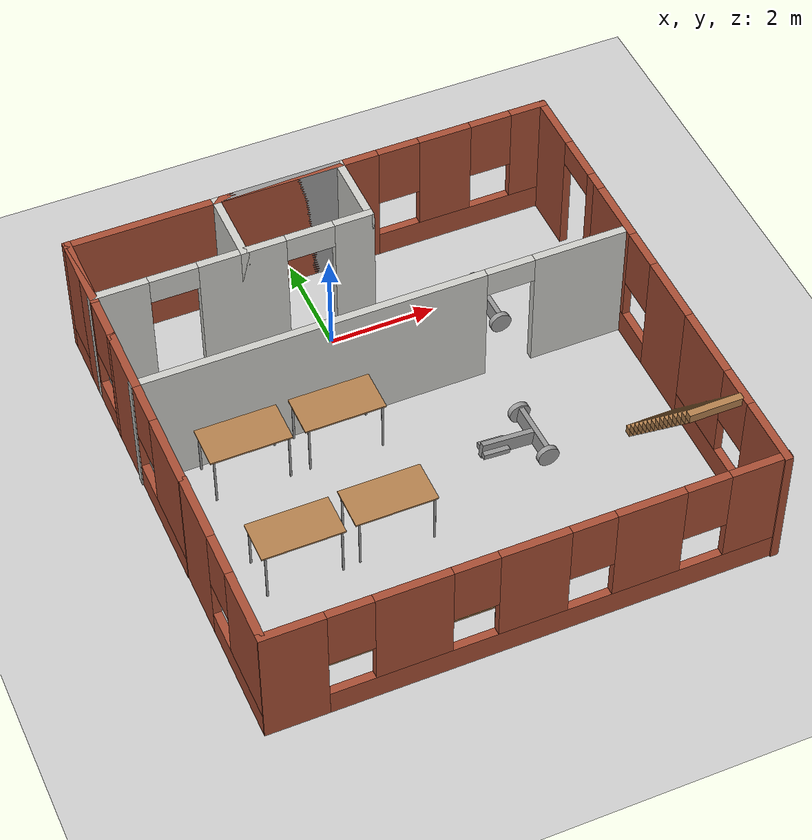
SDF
<sdf version="1.6">
 <world name="default">
  <plugin name="hello" filename="libhello.so"/>
  <light name="sun" type="directional">
   <pose>0 0 10 0 -0 0</pose>
   <diffuse>0.8 0.8 0.8 1</diffuse>
   <specular>0.2 0.2 0.2 1</specular>
   <attenuation>
    <range>1000</range>
    <constant>0.9</constant>
    <linear>0.01</linear>
    <quadratic>0.001</quadratic>
   </attenuation>
   <direction>-0.5 0.1 -0.9</direction>
  </light>
  <model name="ground_plane">
   <static>1</static>
   <link name="link">
    <collision name="collision">
     <geometry><plane><normal>0 0 1</normal><size>100 100</size></plane></geometry>
     <surface>
      <contact><collide_bitmask>65535</collide_bitmask></contact>
      <friction><ode><mu>100</mu><mu2>50</mu2></ode></friction>
     </surface>
    </collision>
    <visual name="visual">
     <cast_shadows>0</cast_shadows>
     <geometry><plane><normal>0 0 1</normal><size>100 100</size></plane></geometry>
     <material>
      <script><uri>file://media/materials/scripts/gazebo.material</uri><name>Gazebo/Grey</name></script>
     </material>
    </visual>
   </link>
  </model>
  <gravity>0 0 -9.8</gravity>
  <magnetic_field>6e-06 2.3e-05 -4.2e-05</magnetic_field>
  <atmosphere type="adiabatic"/>
  <physics name="default_physics" default="0" type="ode">
   <max_step_size>0.001</max_step_size>
   <real_time_factor>1</real_time_factor>
   <real_time_update_rate>1000</real_time_update_rate>
  </physics>
  <scene><ambient>0.4 0.4 0.4 1</ambient><background>0.7 0.7 0.7 1</background><shadows>1</shadows></scene>
  <spherical_coordinates>
   <surface_model>EARTH_WGS84</surface_model>
   <latitude_deg>0</latitude_deg>
   <longitude_deg>0</longitude_deg>
   <elevation>0</elevation>
   <heading_deg>0</heading_deg>
  </spherical_coordinates>
  <model name="table">
   <static>1</static>
   <link name="link">
    <collision name="surface">
     <pose>0 0 1 0 -0 0</pose>
     <geometry><box><size>1.5 0.8 0.03</size></box></geometry>
     <surface><friction><ode><mu>0.6</mu><mu2>0.6</mu2></ode></friction></surface>
    </collision>
    <visual name="visual1">
     <pose>0 0 1 0 -0 0</pose>
     <geometry><box><size>1.5 0.8 0.03</size></box></geometry>
     <material>
      <script><uri>file://media/materials/scripts/gazebo.material</uri><name>Gazebo/Wood</name></script>
     </material>
    </visual>
    <collision name="front_left_leg">
     <pose>0.68 0.38 0.5 0 -0 0</pose>
     <geometry><cylinder><radius>0.02</radius><length>1</length></cylinder></geometry>
    </collision>
    <visual name="front_left_leg">
     <pose>0.68 0.38 0.5 0 -0 0</pose>
     <geometry><cylinder><radius>0.02</radius><length>1</length></cylinder></geometry>
     <material>
      <script><uri>file://media/materials/scripts/gazebo.material</uri><name>Gazebo/Grey</name></script>
     </material>
    </visual>
    <collision name="front_right_leg">
     <pose>0.68 -0.38 0.5 0 -0 0</pose>
     <geometry><cylinder><radius>0.02</radius><length>1</length></cylinder></geometry>
    </collision>
    <visual name="front_right_leg">
     <pose>0.68 -0.38 0.5 0 -0 0</pose>
     <geometry><cylinder><radius>0.02</radius><length>1</length></cylinder></geometry>
     <material>
      <script><uri>file://media/materials/scripts/gazebo.material</uri><name>Gazebo/Grey</name></script>
     </material>
    </visual>
    <collision name="back_right_leg">
     <pose>-0.68 -0.38 0.5 0 -0 0</pose>
     <geometry><cylinder><radius>0.02</radius><length>1</length></cylinder></geometry>
    </collision>
    <visual name="back_right_leg">
     <pose>-0.68 -0.38 0.5 0 -0 0</pose>
     <geometry><cylinder><radius>0.02</radius><length>1</length></cylinder></geometry>
     <material>
      <script><uri>file://media/materials/scripts/gazebo.material</uri><name>Gazebo/Grey</name></script>
     </material>
    </visual>
    <collision name="back_left_leg">
     <pose>-0.68 0.38 0.5 0 -0 0</pose>
     <geometry><cylinder><radius>0.02</radius><length>1</length></cylinder></geometry>
    </collision>
    <visual name="back_left_leg">
     <pose>-0.68 0.38 0.5 0 -0 0</pose>
     <geometry><cylinder><radius>0.02</radius><length>1</length></cylinder></geometry>
     <material>
      <script><uri>file://media/materials/scripts/gazebo.material</uri><name>Gazebo/Grey</name></script>
     </material>
    </visual>
   </link>
   <pose>-0.795331 -2.24058 0 0 -0 0</pose>
  </model>
  <model name="table_0">
   <static>1</static>
   <link name="link">
    <collision name="surface">
     <pose>0 0 1 0 -0 0</pose>
     <geometry><box><size>1.5 0.8 0.03</size></box></geometry>
     <surface><friction><ode><mu>0.6</mu><mu2>0.6</mu2></ode></friction></surface>
    </collision>
    <visual name="visual1">
     <pose>0 0 1 0 -0 0</pose>
     <geometry><box><size>1.5 0.8 0.03</size></box></geometry>
     <material>
      <script><uri>file://media/materials/scripts/gazebo.material</uri><name>Gazebo/Wood</name></script>
     </material>
    </visual>
    <collision name="front_left_leg">
     <pose>0.68 0.38 0.5 0 -0 0</pose>
     <geometry><cylinder><radius>0.02</radius><length>1</length></cylinder></geometry>
    </collision>
    <visual name="front_left_leg">
     <pose>0.68 0.38 0.5 0 -0 0</pose>
     <geometry><cylinder><radius>0.02</radius><length>1</length></cylinder></geometry>
     <material>
      <script><uri>file://media/materials/scripts/gazebo.material</uri><name>Gazebo/Grey</name></script>
     </material>
    </visual>
    <collision name="front_right_leg">
     <pose>0.68 -0.38 0.5 0 -0 0</pose>
     <geometry><cylinder><radius>0.02</radius><length>1</length></cylinder></geometry>
    </collision>
    <visual name="front_right_leg">
     <pose>0.68 -0.38 0.5 0 -0 0</pose>
     <geometry><cylinder><radius>0.02</radius><length>1</length></cylinder></geometry>
     <material>
      <script><uri>file://media/materials/scripts/gazebo.material</uri><name>Gazebo/Grey</name></script>
     </material>
    </visual>
    <collision name="back_right_leg">
     <pose>-0.68 -0.38 0.5 0 -0 0</pose>
     <geometry><cylinder><radius>0.02</radius><length>1</length></cylinder></geometry>
    </collision>
    <visual name="back_right_leg">
     <pose>-0.68 -0.38 0.5 0 -0 0</pose>
     <geometry><cylinder><radius>0.02</radius><length>1</length></cylinder></geometry>
     <material>
      <script><uri>file://media/materials/scripts/gazebo.material</uri><name>Gazebo/Grey</name></script>
     </material>
    </visual>
    <collision name="back_left_leg">
     <pose>-0.68 0.38 0.5 0 -0 0</pose>
     <geometry><cylinder><radius>0.02</radius><length>1</length></cylinder></geometry>
    </collision>
    <visual name="back_left_leg">
     <pose>-0.68 0.38 0.5 0 -0 0</pose>
     <geometry><cylinder><radius>0.02</radius><length>1</length></cylinder></geometry>
     <material>
      <script><uri>file://media/materials/scripts/gazebo.material</uri><name>Gazebo/Grey</name></script>
     </material>
    </visual>
   </link>
   <pose>-2.52213 -2.25429 0 0 -0 0</pose>
  </model>
  <model name="table_1">
   <static>1</static>
   <link name="link">
    <collision name="surface">
     <pose>0 0 1 0 -0 0</pose>
     <geometry><box><size>1.5 0.8 0.03</size></box></geometry>
     <surface><friction><ode><mu>0.6</mu><mu2>0.6</mu2></ode></friction></surface>
    </collision>
    <visual name="visual1">
     <pose>0 0 1 0 -0 0</pose>
     <geometry><box><size>1.5 0.8 0.03</size></box></geometry>
     <material>
      <script><uri>file://media/materials/scripts/gazebo.material</uri><name>Gazebo/Wood</name></script>
     </material>
    </visual>
    <collision name="front_left_leg">
     <pose>0.68 0.38 0.5 0 -0 0</pose>
     <geometry><cylinder><radius>0.02</radius><length>1</length></cylinder></geometry>
    </collision>
    <visual name="front_left_leg">
     <pose>0.68 0.38 0.5 0 -0 0</pose>
     <geometry><cylinder><radius>0.02</radius><length>1</length></cylinder></geometry>
     <material>
      <script><uri>file://media/materials/scripts/gazebo.material</uri><name>Gazebo/Grey</name></script>
     </material>
    </visual>
    <collision name="front_right_leg">
     <pose>0.68 -0.38 0.5 0 -0 0</pose>
     <geometry><cylinder><radius>0.02</radius><length>1</length></cylinder></geometry>
    </collision>
    <visual name="front_right_leg">
     <pose>0.68 -0.38 0.5 0 -0 0</pose>
     <geometry><cylinder><radius>0.02</radius><length>1</length></cylinder></geometry>
     <material>
      <script><uri>file://media/materials/scripts/gazebo.material</uri><name>Gazebo/Grey</name></script>
     </material>
    </visual>
    <collision name="back_right_leg">
     <pose>-0.68 -0.38 0.5 0 -0 0</pose>
     <geometry><cylinder><radius>0.02</radius><length>1</length></cylinder></geometry>
    </collision>
    <visual name="back_right_leg">
     <pose>-0.68 -0.38 0.5 0 -0 0</pose>
     <geometry><cylinder><radius>0.02</radius><length>1</length></cylinder></geometry>
     <material>
      <script><uri>file://media/materials/scripts/gazebo.material</uri><name>Gazebo/Grey</name></script>
     </material>
    </visual>
    <collision name="back_left_leg">
     <pose>-0.68 0.38 0.5 0 -0 0</pose>
     <geometry><cylinder><radius>0.02</radius><length>1</length></cylinder></geometry>
    </collision>
    <visual name="back_left_leg">
     <pose>-0.68 0.38 0.5 0 -0 0</pose>
     <geometry><cylinder><radius>0.02</radius><length>1</length></cylinder></geometry>
     <material>
      <script><uri>file://media/materials/scripts/gazebo.material</uri><name>Gazebo/Grey</name></script>
     </material>
    </visual>
   </link>
   <pose>-0.78676 -6.88535 0 0 -0 0</pose>
  </model>
  <model name="table_2">
   <static>1</static>
   <link name="link">
    <collision name="surface">
     <pose>0 0 1 0 -0 0</pose>
     <geometry><box><size>1.5 0.8 0.03</size></box></geometry>
     <surface><friction><ode><mu>0.6</mu><mu2>0.6</mu2></ode></friction></surface>
    </collision>
    <visual name="visual1">
     <pose>0 0 1 0 -0 0</pose>
     <geometry><box><size>1.5 0.8 0.03</size></box></geometry>
     <material>
      <script><uri>file://media/materials/scripts/gazebo.material</uri><name>Gazebo/Wood</name></script>
     </material>
    </visual>
    <collision name="front_left_leg">
     <pose>0.68 0.38 0.5 0 -0 0</pose>
     <geometry><cylinder><radius>0.02</radius><length>1</length></cylinder></geometry>
    </collision>
    <visual name="front_left_leg">
     <pose>0.68 0.38 0.5 0 -0 0</pose>
     <geometry><cylinder><radius>0.02</radius><length>1</length></cylinder></geometry>
     <material>
      <script><uri>file://media/materials/scripts/gazebo.material</uri><name>Gazebo/Grey</name></script>
     </material>
    </visual>
    <collision name="front_right_leg">
     <pose>0.68 -0.38 0.5 0 -0 0</pose>
     <geometry><cylinder><radius>0.02</radius><length>1</length></cylinder></geometry>
    </collision>
    <visual name="front_right_leg">
     <pose>0.68 -0.38 0.5 0 -0 0</pose>
     <geometry><cylinder><radius>0.02</radius><length>1</length></cylinder></geometry>
     <material>
      <script><uri>file://media/materials/scripts/gazebo.material</uri><name>Gazebo/Grey</name></script>
     </material>
    </visual>
    <collision name="back_right_leg">
     <pose>-0.68 -0.38 0.5 0 -0 0</pose>
     <geometry><cylinder><radius>0.02</radius><length>1</length></cylinder></geometry>
    </collision>
    <visual name="back_right_leg">
     <pose>-0.68 -0.38 0.5 0 -0 0</pose>
     <geometry><cylinder><radius>0.02</radius><length>1</length></cylinder></geometry>
     <material>
      <script><uri>file://media/materials/scripts/gazebo.material</uri><name>Gazebo/Grey</name></script>
     </material>
    </visual>
    <collision name="back_left_leg">
     <pose>-0.68 0.38 0.5 0 -0 0</pose>
     <geometry><cylinder><radius>0.02</radius><length>1</length></cylinder></geometry>
    </collision>
    <visual name="back_left_leg">
     <pose>-0.68 0.38 0.5 0 -0 0</pose>
     <geometry><cylinder><radius>0.02</radius><length>1</length></cylinder></geometry>
     <material>
      <script><uri>file://media/materials/scripts/gazebo.material</uri><name>Gazebo/Grey</name></script>
     </material>
    </visual>
   </link>
   <pose>-2.5066 -6.87223 0 0 -0 0</pose>
  </model>
  <model name="robot_with_arms">
   <link name="link_0">
    <inertial>
     <mass>1</mass>
     <inertia>
      <ixx>0.166667</ixx>
      <ixy>0</ixy>
      <ixz>0</ixz>
      <iyy>0.166667</iyy>
      <iyz>0</iyz>
      <izz>0.166667</izz>
     </inertia>
    </inertial>
    <visual name="visual">
     <geometry><box><size>0.3 1 0.1</size></box></geometry>
     <material>
      <lighting>1</lighting>
      <script><uri>file://media/materials/scripts/gazebo.material</uri><name>Gazebo/Grey</name></script>
      <shader type="pixel"><normal_map>__default__</normal_map></shader>
      <ambient>0.3 0.3 0.3 1</ambient>
      <diffuse>0.7 0.7 0.7 1</diffuse>
      <specular>0.01 0.01 0.01 1</specular>
      <emissive>0 0 0 1</emissive>
     </material>
    </visual>
    <visual name="ModelPreview_0::link_0::visual_1">
     <geometry><box><size>0.3 1 0.1</size></box></geometry>
     <material>
      <lighting>1</lighting>
      <script><uri>file://media/materials/scripts/gazebo.material</uri><name>Gazebo/Grey</name></script>
      <shader type="pixel"><normal_map>__default__</normal_map></shader>
      <ambient>0.3 0.3 0.3 1</ambient>
      <diffuse>0.7 0.7 0.7 1</diffuse>
      <specular>0.01 0.01 0.01 1</specular>
      <emissive>0 0 0 1</emissive>
     </material>
    </visual>
    <collision name="collision">
     <geometry><box><size>0.3 1 0.1</size></box></geometry>
     <surface>
      <friction>
       <ode><mu>1</mu><mu2>1</mu2><fdir1>0 0 0</fdir1><slip1>0</slip1><slip2>0</slip2></ode>
       <torsional>
        <coefficient>1</coefficient>
        <patch_radius>0</patch_radius>
        <surface_radius>0</surface_radius>
        <use_patch_radius>1</use_patch_radius>
        <ode><slip>0</slip></ode>
       </torsional>
      </friction>
      <bounce><restitution_coefficient>0</restitution_coefficient><threshold>1e+06</threshold></bounce>
      <contact>
       <collide_without_contact>0</collide_without_contact>
       <collide_without_contact_bitmask>1</collide_without_contact_bitmask>
       <collide_bitmask>1</collide_bitmask>
       <ode>
        <soft_cfm>0</soft_cfm>
        <soft_erp>0.2</soft_erp>
        <kp>1e+13</kp>
        <kd>1</kd>
        <max_vel>0.01</max_vel>
        <min_depth>0</min_depth>
       </ode>
       <bullet>
        <split_impulse>1</split_impulse>
        <split_impulse_penetration_threshold>-0.01</split_impulse_penetration_threshold>
        <soft_cfm>0</soft_cfm>
        <soft_erp>0.2</soft_erp>
        <kp>1e+13</kp>
        <kd>1</kd>
       </bullet>
      </contact>
     </surface>
    </collision>
   </link>
   <link name="link_0_0">
    <pose>-0 -0.045 0.55 0 -0 0</pose>
    <inertial>
     <mass>1</mass>
     <inertia>
      <ixx>0.166667</ixx>
      <ixy>0</ixy>
      <ixz>0</ixz>
      <iyy>0.166667</iyy>
      <iyz>0</iyz>
      <izz>0.166667</izz>
     </inertia>
    </inertial>
    <visual name="visual">
     <geometry><box><size>0.3 0.1 1</size></box></geometry>
     <material>
      <lighting>1</lighting>
      <script><uri>file://media/materials/scripts/gazebo.material</uri><name>Gazebo/Grey</name></script>
      <shader type="pixel"><normal_map>__default__</normal_map></shader>
      <ambient>0.3 0.3 0.3 1</ambient>
      <diffuse>0.7 0.7 0.7 1</diffuse>
      <specular>0.01 0.01 0.01 1</specular>
      <emissive>0 0 0 1</emissive>
     </material>
    </visual>
    <collision name="collision">
     <geometry><box><size>0.3 0.1 1</size></box></geometry>
     <surface>
      <friction>
       <ode><mu>1</mu><mu2>1</mu2><fdir1>0 0 0</fdir1><slip1>0</slip1><slip2>0</slip2></ode>
       <torsional>
        <coefficient>1</coefficient>
        <patch_radius>0</patch_radius>
        <surface_radius>0</surface_radius>
        <use_patch_radius>1</use_patch_radius>
        <ode><slip>0</slip></ode>
       </torsional>
      </friction>
      <bounce><restitution_coefficient>0</restitution_coefficient><threshold>1e+06</threshold></bounce>
      <contact>
       <collide_without_contact>0</collide_without_contact>
       <collide_without_contact_bitmask>1</collide_without_contact_bitmask>
       <collide_bitmask>1</collide_bitmask>
       <ode>
        <soft_cfm>0</soft_cfm>
        <soft_erp>0.2</soft_erp>
        <kp>1e+13</kp>
        <kd>1</kd>
        <max_vel>0.01</max_vel>
        <min_depth>0</min_depth>
       </ode>
       <bullet>
        <split_impulse>1</split_impulse>
        <split_impulse_penetration_threshold>-0.01</split_impulse_penetration_threshold>
        <soft_cfm>0</soft_cfm>
        <soft_erp>0.2</soft_erp>
        <kp>1e+13</kp>
        <kd>1</kd>
       </bullet>
      </contact>
     </surface>
    </collision>
   </link>
   <link name="link_1">
    <pose>0 -0.550019 -0 1.5707 -0 0</pose>
    <inertial>
     <mass>1</mass>
     <inertia><ixx>0.145833</ixx><ixy>0</ixy><ixz>0</ixz><iyy>0.145833</iyy><iyz>0</iyz><izz>0.125</izz></inertia>
    </inertial>
    <visual name="visual">
     <geometry><cylinder><radius>0.2</radius><length>0.1</length></cylinder></geometry>
     <material>
      <lighting>1</lighting>
      <script><uri>file://media/materials/scripts/gazebo.material</uri><name>Gazebo/Grey</name></script>
      <shader type="pixel"><normal_map>__default__</normal_map></shader>
      <ambient>0.3 0.3 0.3 1</ambient>
      <diffuse>0.7 0.7 0.7 1</diffuse>
      <specular>0.01 0.01 0.01 1</specular>
      <emissive>0 0 0 1</emissive>
     </material>
    </visual>
    <collision name="collision">
     <geometry><cylinder><radius>0.2</radius><length>0.1</length></cylinder></geometry>
     <surface>
      <friction>
       <ode><mu>1</mu><mu2>1</mu2><fdir1>0 0 0</fdir1><slip1>0</slip1><slip2>0</slip2></ode>
       <torsional>
        <coefficient>1</coefficient>
        <patch_radius>0</patch_radius>
        <surface_radius>0</surface_radius>
        <use_patch_radius>1</use_patch_radius>
        <ode><slip>0</slip></ode>
       </torsional>
      </friction>
      <bounce><restitution_coefficient>0</restitution_coefficient><threshold>1e+06</threshold></bounce>
      <contact>
       <collide_without_contact>0</collide_without_contact>
       <collide_without_contact_bitmask>1</collide_without_contact_bitmask>
       <collide_bitmask>1</collide_bitmask>
       <ode>
        <soft_cfm>0</soft_cfm>
        <soft_erp>0.2</soft_erp>
        <kp>1e+13</kp>
        <kd>1</kd>
        <max_vel>0.01</max_vel>
        <min_depth>0</min_depth>
       </ode>
       <bullet>
        <split_impulse>1</split_impulse>
        <split_impulse_penetration_threshold>-0.01</split_impulse_penetration_threshold>
        <soft_cfm>0</soft_cfm>
        <soft_erp>0.2</soft_erp>
        <kp>1e+13</kp>
        <kd>1</kd>
       </bullet>
      </contact>
     </surface>
    </collision>
   </link>
   <link name="link_1_0">
    <pose>-0.045 -0.145 0.8 0 -0 0</pose>
    <inertial>
     <mass>1</mass>
     <inertia>
      <ixx>0.166667</ixx>
      <ixy>0</ixy>
      <ixz>0</ixz>
      <iyy>0.166667</iyy>
      <iyz>0</iyz>
      <izz>0.166667</izz>
     </inertia>
    </inertial>
    <visual name="visual">
     <geometry><box><size>0.1 0.1 0.5</size></box></geometry>
     <material>
      <lighting>1</lighting>
      <script><uri>file://media/materials/scripts/gazebo.material</uri><name>Gazebo/Grey</name></script>
      <shader type="pixel"><normal_map>__default__</normal_map></shader>
      <ambient>0.3 0.3 0.3 1</ambient>
      <diffuse>0.7 0.7 0.7 1</diffuse>
      <specular>0.01 0.01 0.01 1</specular>
      <emissive>0 0 0 1</emissive>
     </material>
    </visual>
    <collision name="collision">
     <geometry><box><size>0.1 0.1 0.5</size></box></geometry>
     <surface>
      <friction>
       <ode><mu>1</mu><mu2>1</mu2><fdir1>0 0 0</fdir1><slip1>0</slip1><slip2>0</slip2></ode>
       <torsional>
        <coefficient>1</coefficient>
        <patch_radius>0</patch_radius>
        <surface_radius>0</surface_radius>
        <use_patch_radius>1</use_patch_radius>
        <ode><slip>0</slip></ode>
       </torsional>
      </friction>
      <bounce><restitution_coefficient>0</restitution_coefficient><threshold>1e+06</threshold></bounce>
      <contact>
       <collide_without_contact>0</collide_without_contact>
       <collide_without_contact_bitmask>1</collide_without_contact_bitmask>
       <collide_bitmask>1</collide_bitmask>
       <ode>
        <soft_cfm>0</soft_cfm>
        <soft_erp>0.2</soft_erp>
        <kp>1e+13</kp>
        <kd>1</kd>
        <max_vel>0.01</max_vel>
        <min_depth>0</min_depth>
       </ode>
       <bullet>
        <split_impulse>1</split_impulse>
        <split_impulse_penetration_threshold>-0.01</split_impulse_penetration_threshold>
        <soft_cfm>0</soft_cfm>
        <soft_erp>0.2</soft_erp>
        <kp>1e+13</kp>
        <kd>1</kd>
       </bullet>
      </contact>
     </surface>
    </collision>
   </link>
   <link name="link_1_0_clone">
    <pose>-0 0.055 0.8 0 -0 0</pose>
    <inertial>
     <mass>1</mass>
     <inertia>
      <ixx>0.166667</ixx>
      <ixy>0</ixy>
      <ixz>0</ixz>
      <iyy>0.166667</iyy>
      <iyz>0</iyz>
      <izz>0.166667</izz>
     </inertia>
    </inertial>
    <visual name="visual_0">
     <geometry><box><size>0.1 0.1 0.5</size></box></geometry>
     <material>
      <lighting>1</lighting>
      <script><uri>file://media/materials/scripts/gazebo.material</uri><name>Gazebo/Grey</name></script>
      <shader type="pixel"><normal_map>__default__</normal_map></shader>
      <ambient>0.3 0.3 0.3 1</ambient>
      <diffuse>0.7 0.7 0.7 1</diffuse>
      <specular>0.01 0.01 0.01 1</specular>
      <emissive>0 0 0 1</emissive>
     </material>
    </visual>
    <collision name="collision">
     <geometry><box><size>0.1 0.1 0.5</size></box></geometry>
     <surface>
      <friction>
       <ode><mu>1</mu><mu2>1</mu2><fdir1>0 0 0</fdir1><slip1>0</slip1><slip2>0</slip2></ode>
       <torsional>
        <coefficient>1</coefficient>
        <patch_radius>0</patch_radius>
        <surface_radius>0</surface_radius>
        <use_patch_radius>1</use_patch_radius>
        <ode><slip>0</slip></ode>
       </torsional>
      </friction>
      <bounce><restitution_coefficient>0</restitution_coefficient><threshold>1e+06</threshold></bounce>
      <contact>
       <collide_without_contact>0</collide_without_contact>
       <collide_without_contact_bitmask>1</collide_without_contact_bitmask>
       <collide_bitmask>1</collide_bitmask>
       <ode>
        <soft_cfm>0</soft_cfm>
        <soft_erp>0.2</soft_erp>
        <kp>1e+13</kp>
        <kd>1</kd>
        <max_vel>0.01</max_vel>
        <min_depth>0</min_depth>
       </ode>
       <bullet>
        <split_impulse>1</split_impulse>
        <split_impulse_penetration_threshold>-0.01</split_impulse_penetration_threshold>
        <soft_cfm>0</soft_cfm>
        <soft_erp>0.2</soft_erp>
        <kp>1e+13</kp>
        <kd>1</kd>
       </bullet>
      </contact>
     </surface>
    </collision>
   </link>
   <link name="link_1_clone">
    <pose>-0 0.550019 0 1.5707 -0 0</pose>
    <inertial>
     <mass>1</mass>
     <inertia><ixx>0.145833</ixx><ixy>0</ixy><ixz>0</ixz><iyy>0.145833</iyy><iyz>0</iyz><izz>0.125</izz></inertia>
    </inertial>
    <visual name="visual">
     <geometry><cylinder><radius>0.2</radius><length>0.1</length></cylinder></geometry>
     <material>
      <lighting>1</lighting>
      <script><uri>file://media/materials/scripts/gazebo.material</uri><name>Gazebo/Grey</name></script>
      <shader type="pixel"><normal_map>__default__</normal_map></shader>
      <ambient>0.3 0.3 0.3 1</ambient>
      <diffuse>0.7 0.7 0.7 1</diffuse>
      <specular>0.01 0.01 0.01 1</specular>
      <emissive>0 0 0 1</emissive>
     </material>
    </visual>
    <collision name="collision">
     <geometry><cylinder><radius>0.2</radius><length>0.1</length></cylinder></geometry>
     <surface>
      <friction>
       <ode><mu>1</mu><mu2>1</mu2><fdir1>0 0 0</fdir1><slip1>0</slip1><slip2>0</slip2></ode>
       <torsional>
        <coefficient>1</coefficient>
        <patch_radius>0</patch_radius>
        <surface_radius>0</surface_radius>
        <use_patch_radius>1</use_patch_radius>
        <ode><slip>0</slip></ode>
       </torsional>
      </friction>
      <bounce><restitution_coefficient>0</restitution_coefficient><threshold>1e+06</threshold></bounce>
      <contact>
       <collide_without_contact>0</collide_without_contact>
       <collide_without_contact_bitmask>1</collide_without_contact_bitmask>
       <collide_bitmask>1</collide_bitmask>
       <ode>
        <soft_cfm>0</soft_cfm>
        <soft_erp>0.2</soft_erp>
        <kp>1e+13</kp>
        <kd>1</kd>
        <max_vel>0.01</max_vel>
        <min_depth>0</min_depth>
       </ode>
       <bullet>
        <split_impulse>1</split_impulse>
        <split_impulse_penetration_threshold>-0.01</split_impulse_penetration_threshold>
        <soft_cfm>0</soft_cfm>
        <soft_erp>0.2</soft_erp>
        <kp>1e+13</kp>
        <kd>1</kd>
       </bullet>
      </contact>
     </surface>
    </collision>
   </link>
   <joint name="link_0_0_JOINT_1" type="revolute">
    <parent>link_0_0</parent>
    <child>link_1_0</child>
    <axis>
     <xyz>0 1 0</xyz>
     <use_parent_model_frame>0</use_parent_model_frame>
     <limit>
      <lower>-1.79769e+308</lower>
      <upper>1.79769e+308</upper>
      <effort>-1</effort>
      <velocity>-1</velocity>
     </limit>
     <dynamics>
      <spring_reference>0</spring_reference>
      <spring_stiffness>0</spring_stiffness>
      <damping>0</damping>
      <friction>0</friction>
     </dynamics>
    </axis>
    <physics>
     <ode><limit><cfm>0</cfm><erp>0.2</erp></limit><suspension><cfm>0</cfm><erp>0.2</erp></suspension></ode>
    </physics>
   </joint>
   <joint name="link_0_0_JOINT_2" type="revolute">
    <parent>link_0_0</parent>
    <child>link_1_0_clone</child>
    <axis>
     <xyz>0 1 0</xyz>
     <use_parent_model_frame>0</use_parent_model_frame>
     <limit>
      <lower>-1.79769e+308</lower>
      <upper>1.79769e+308</upper>
      <effort>-1</effort>
      <velocity>-1</velocity>
     </limit>
     <dynamics>
      <spring_reference>0</spring_reference>
      <spring_stiffness>0</spring_stiffness>
      <damping>0</damping>
      <friction>0</friction>
     </dynamics>
    </axis>
    <physics>
     <ode><limit><cfm>0</cfm><erp>0.2</erp></limit><suspension><cfm>0</cfm><erp>0.2</erp></suspension></ode>
    </physics>
   </joint>
   <joint name="link_0_JOINT_0_0" type="fixed">
    <parent>link_0</parent>
    <child>link_0_0</child>
    <physics>
     <ode><limit><cfm>0</cfm><erp>0.2</erp></limit><suspension><cfm>0</cfm><erp>0.2</erp></suspension></ode>
    </physics>
   </joint>
   <joint name="link_0_JOINT_0" type="revolute">
    <parent>link_0</parent>
    <child>link_1</child>
    <axis>
     <xyz>0 0 1</xyz>
     <use_parent_model_frame>0</use_parent_model_frame>
     <limit>
      <lower>-1.79769e+308</lower>
      <upper>1.79769e+308</upper>
      <effort>-1</effort>
      <velocity>-1</velocity>
     </limit>
     <dynamics>
      <spring_reference>0</spring_reference>
      <spring_stiffness>0</spring_stiffness>
      <damping>0</damping>
      <friction>0</friction>
     </dynamics>
    </axis>
    <physics>
     <ode><limit><cfm>0</cfm><erp>0.2</erp></limit><suspension><cfm>0</cfm><erp>0.2</erp></suspension></ode>
    </physics>
   </joint>
   <joint name="link_0_JOINT_1" type="revolute">
    <parent>link_0</parent>
    <child>link_1_clone</child>
    <axis>
     <xyz>0 0 1</xyz>
     <use_parent_model_frame>0</use_parent_model_frame>
     <limit>
      <lower>-1.79769e+308</lower>
      <upper>1.79769e+308</upper>
      <effort>-1</effort>
      <velocity>-1</velocity>
     </limit>
     <dynamics>
      <spring_reference>0</spring_reference>
      <spring_stiffness>0</spring_stiffness>
      <damping>0</damping>
      <friction>0</friction>
     </dynamics>
    </axis>
    <physics>
     <ode><limit><cfm>0</cfm><erp>0.2</erp></limit><suspension><cfm>0</cfm><erp>0.2</erp></suspension></ode>
    </physics>
   </joint>
   <static>0</static>
   <pose>2.88559 -0.390082 0.199998 -2.6e-05 -1.45216 0.030132</pose>
  </model>
  <model name="Building">
   <link name="Stairs_1">
    <pose>0.046334 -2.64714 0 0 -0 0</pose>
    <visual name="Stairs_1_Visual_3">
     <pose>3.95843 -0.779973 0.583333 0 -0 0</pose>
     <geometry><box><size>1 0.133333 0.166667</size></box></geometry>
     <material>
      <script><uri>file://media/materials/scripts/gazebo.material</uri><name>Gazebo/Wood</name></script>
      <ambient>1 1 1 1</ambient>
      <shader type="pixel"/>
      <diffuse>1 1 1 1</diffuse>
      <specular>0.2 0.2 0.2 1</specular>
      <emissive>0 0 0 1</emissive>
     </material>
     <meta><layer>0</layer></meta>
    </visual>
    <visual name="Stairs_1_Visual_0">
     <pose>3.95843 -0.379973 0.083333 0 -0 0</pose>
     <geometry><box><size>1 0.133333 0.166667</size></box></geometry>
     <material>
      <script><uri>file://media/materials/scripts/gazebo.material</uri><name>Gazebo/Wood</name></script>
      <ambient>1 1 1 1</ambient>
      <shader type="pixel"/>
      <diffuse>1 1 1 1</diffuse>
      <specular>0.2 0.2 0.2 1</specular>
      <emissive>0 0 0 1</emissive>
     </material>
     <meta><layer>0</layer></meta>
    </visual>
    <visual name="Stairs_1_Visual_4">
     <pose>3.95843 -0.913306 0.75 0 -0 0</pose>
     <geometry><box><size>1 0.133333 0.166667</size></box></geometry>
     <material>
      <script><uri>file://media/materials/scripts/gazebo.material</uri><name>Gazebo/Wood</name></script>
      <ambient>1 1 1 1</ambient>
      <shader type="pixel"/>
      <diffuse>1 1 1 1</diffuse>
      <specular>0.2 0.2 0.2 1</specular>
      <emissive>0 0 0 1</emissive>
     </material>
     <meta><layer>0</layer></meta>
    </visual>
    <visual name="Stairs_1_Visual_2">
     <pose>3.95843 -0.646639 0.416667 0 -0 0</pose>
     <geometry><box><size>1 0.133333 0.166667</size></box></geometry>
     <material>
      <script><uri>file://media/materials/scripts/gazebo.material</uri><name>Gazebo/Wood</name></script>
      <ambient>1 1 1 1</ambient>
      <shader type="pixel"/>
      <diffuse>1 1 1 1</diffuse>
      <specular>0.2 0.2 0.2 1</specular>
      <emissive>0 0 0 1</emissive>
     </material>
     <meta><layer>0</layer></meta>
    </visual>
    <visual name="Stairs_1_Visual_5">
     <pose>3.95843 -1.04664 0.916667 0 -0 0</pose>
     <geometry><box><size>1 0.133333 0.166667</size></box></geometry>
     <material>
      <script><uri>file://media/materials/scripts/gazebo.material</uri><name>Gazebo/Wood</name></script>
      <ambient>1 1 1 1</ambient>
      <shader type="pixel"/>
      <diffuse>1 1 1 1</diffuse>
      <specular>0.2 0.2 0.2 1</specular>
      <emissive>0 0 0 1</emissive>
     </material>
     <meta><layer>0</layer></meta>
    </visual>
    <visual name="Stairs_1_Visual_6">
     <pose>3.95843 -1.17997 1.08333 0 -0 0</pose>
     <geometry><box><size>1 0.133333 0.166667</size></box></geometry>
     <material>
      <script><uri>file://media/materials/scripts/gazebo.material</uri><name>Gazebo/Wood</name></script>
      <ambient>1 1 1 1</ambient>
      <shader type="pixel"/>
      <diffuse>1 1 1 1</diffuse>
      <specular>0.2 0.2 0.2 1</specular>
      <emissive>0 0 0 1</emissive>
     </material>
     <meta><layer>0</layer></meta>
    </visual>
    <visual name="Stairs_1_Visual_7">
     <pose>3.95843 -1.31331 1.25 0 -0 0</pose>
     <geometry><box><size>1 0.133333 0.166667</size></box></geometry>
     <material>
      <script><uri>file://media/materials/scripts/gazebo.material</uri><name>Gazebo/Wood</name></script>
      <ambient>1 1 1 1</ambient>
      <shader type="pixel"/>
      <diffuse>1 1 1 1</diffuse>
      <specular>0.2 0.2 0.2 1</specular>
      <emissive>0 0 0 1</emissive>
     </material>
     <meta><layer>0</layer></meta>
    </visual>
    <visual name="Stairs_1_Visual_12">
     <pose>3.95843 -1.97997 2.08333 0 -0 0</pose>
     <geometry><box><size>1 0.133333 0.166667</size></box></geometry>
     <material>
      <script><uri>file://media/materials/scripts/gazebo.material</uri><name>Gazebo/Wood</name></script>
      <ambient>1 1 1 1</ambient>
      <shader type="pixel"/>
      <diffuse>1 1 1 1</diffuse>
      <specular>0.2 0.2 0.2 1</specular>
      <emissive>0 0 0 1</emissive>
     </material>
     <meta><layer>0</layer></meta>
    </visual>
    <visual name="Stairs_1_Visual_13">
     <pose>3.95843 -2.11331 2.25 0 -0 0</pose>
     <geometry><box><size>1 0.133333 0.166667</size></box></geometry>
     <material>
      <script><uri>file://media/materials/scripts/gazebo.material</uri><name>Gazebo/Wood</name></script>
      <ambient>1 1 1 1</ambient>
      <shader type="pixel"/>
      <diffuse>1 1 1 1</diffuse>
      <specular>0.2 0.2 0.2 1</specular>
      <emissive>0 0 0 1</emissive>
     </material>
     <meta><layer>0</layer></meta>
    </visual>
    <visual name="Stairs_1_Visual_14">
     <pose>3.95843 -2.24664 2.41667 0 -0 0</pose>
     <geometry><box><size>1 0.133333 0.166667</size></box></geometry>
     <material>
      <script><uri>file://media/materials/scripts/gazebo.material</uri><name>Gazebo/Wood</name></script>
      <ambient>1 1 1 1</ambient>
      <shader type="pixel"/>
      <diffuse>1 1 1 1</diffuse>
      <specular>0.2 0.2 0.2 1</specular>
      <emissive>0 0 0 1</emissive>
     </material>
     <meta><layer>0</layer></meta>
    </visual>
    <visual name="Stairs_1_Visual_8">
     <pose>3.95843 -1.44664 1.41667 0 -0 0</pose>
     <geometry><box><size>1 0.133333 0.166667</size></box></geometry>
     <material>
      <script><uri>file://media/materials/scripts/gazebo.material</uri><name>Gazebo/Wood</name></script>
      <ambient>1 1 1 1</ambient>
      <shader type="pixel"/>
      <diffuse>1 1 1 1</diffuse>
      <specular>0.2 0.2 0.2 1</specular>
      <emissive>0 0 0 1</emissive>
     </material>
     <meta><layer>0</layer></meta>
    </visual>
    <visual name="Stairs_1_Visual_9">
     <pose>3.95843 -1.57997 1.58333 0 -0 0</pose>
     <geometry><box><size>1 0.133333 0.166667</size></box></geometry>
     <material>
      <script><uri>file://media/materials/scripts/gazebo.material</uri><name>Gazebo/Wood</name></script>
      <ambient>1 1 1 1</ambient>
      <shader type="pixel"/>
      <diffuse>1 1 1 1</diffuse>
      <specular>0.2 0.2 0.2 1</specular>
      <emissive>0 0 0 1</emissive>
     </material>
     <meta><layer>0</layer></meta>
    </visual>
    <visual name="Stairs_1_Visual_10">
     <pose>3.95843 -1.71331 1.75 0 -0 0</pose>
     <geometry><box><size>1 0.133333 0.166667</size></box></geometry>
     <material>
      <script><uri>file://media/materials/scripts/gazebo.material</uri><name>Gazebo/Wood</name></script>
      <ambient>1 1 1 1</ambient>
      <shader type="pixel"/>
      <diffuse>1 1 1 1</diffuse>
      <specular>0.2 0.2 0.2 1</specular>
      <emissive>0 0 0 1</emissive>
     </material>
     <meta><layer>0</layer></meta>
    </visual>
    <visual name="Stairs_1_Visual_11">
     <pose>3.95843 -1.84664 1.91667 0 -0 0</pose>
     <geometry><box><size>1 0.133333 0.166667</size></box></geometry>
     <material>
      <script><uri>file://media/materials/scripts/gazebo.material</uri><name>Gazebo/Wood</name></script>
      <ambient>1 1 1 1</ambient>
      <shader type="pixel"/>
      <diffuse>1 1 1 1</diffuse>
      <specular>0.2 0.2 0.2 1</specular>
      <emissive>0 0 0 1</emissive>
     </material>
     <meta><layer>0</layer></meta>
    </visual>
    <visual name="Stairs_1_Visual_1">
     <pose>3.95843 -0.513306 0.25 0 -0 0</pose>
     <geometry><box><size>1 0.133333 0.166667</size></box></geometry>
     <material>
      <script><uri>file://media/materials/scripts/gazebo.material</uri><name>Gazebo/Wood</name></script>
      <ambient>1 1 1 1</ambient>
      <shader type="pixel"/>
      <diffuse>1 1 1 1</diffuse>
      <specular>0.2 0.2 0.2 1</specular>
      <emissive>0 0 0 1</emissive>
     </material>
     <meta><layer>0</layer></meta>
    </visual>
    <collision name="Stairs_1_Collision_4">
     <pose>3.95843 -0.913306 0.75 0 -0 0</pose>
     <geometry><box><size>1 0.133333 0.166667</size></box></geometry>
     <surface>
      <friction>
       <ode><mu>1</mu><mu2>1</mu2><fdir1>0 0 0</fdir1><slip1>0</slip1><slip2>0</slip2></ode>
       <torsional>
        <coefficient>1</coefficient>
        <patch_radius>0</patch_radius>
        <surface_radius>0</surface_radius>
        <use_patch_radius>1</use_patch_radius>
        <ode><slip>0</slip></ode>
       </torsional>
      </friction>
      <bounce><restitution_coefficient>0</restitution_coefficient><threshold>1e+06</threshold></bounce>
      <contact>
       <collide_without_contact>0</collide_without_contact>
       <collide_without_contact_bitmask>1</collide_without_contact_bitmask>
       <collide_bitmask>1</collide_bitmask>
       <ode>
        <soft_cfm>0</soft_cfm>
        <soft_erp>0.2</soft_erp>
        <kp>1e+13</kp>
        <kd>1</kd>
        <max_vel>0.01</max_vel>
        <min_depth>0</min_depth>
       </ode>
       <bullet>
        <split_impulse>1</split_impulse>
        <split_impulse_penetration_threshold>-0.01</split_impulse_penetration_threshold>
        <soft_cfm>0</soft_cfm>
        <soft_erp>0.2</soft_erp>
        <kp>1e+13</kp>
        <kd>1</kd>
       </bullet>
      </contact>
     </surface>
    </collision>
    <collision name="Stairs_1_Collision_0">
     <pose>3.95843 -0.379973 0.083333 0 -0 0</pose>
     <geometry><box><size>1 0.133333 0.166667</size></box></geometry>
     <surface>
      <friction>
       <ode><mu>1</mu><mu2>1</mu2><fdir1>0 0 0</fdir1><slip1>0</slip1><slip2>0</slip2></ode>
       <torsional>
        <coefficient>1</coefficient>
        <patch_radius>0</patch_radius>
        <surface_radius>0</surface_radius>
        <use_patch_radius>1</use_patch_radius>
        <ode><slip>0</slip></ode>
       </torsional>
      </friction>
      <bounce><restitution_coefficient>0</restitution_coefficient><threshold>1e+06</threshold></bounce>
      <contact>
       <collide_without_contact>0</collide_without_contact>
       <collide_without_contact_bitmask>1</collide_without_contact_bitmask>
       <collide_bitmask>1</collide_bitmask>
       <ode>
        <soft_cfm>0</soft_cfm>
        <soft_erp>0.2</soft_erp>
        <kp>1e+13</kp>
        <kd>1</kd>
        <max_vel>0.01</max_vel>
        <min_depth>0</min_depth>
       </ode>
       <bullet>
        <split_impulse>1</split_impulse>
        <split_impulse_penetration_threshold>-0.01</split_impulse_penetration_threshold>
        <soft_cfm>0</soft_cfm>
        <soft_erp>0.2</soft_erp>
        <kp>1e+13</kp>
        <kd>1</kd>
       </bullet>
      </contact>
     </surface>
    </collision>
    <collision name="Stairs_1_Collision_3">
     <pose>3.95843 -0.779973 0.583333 0 -0 0</pose>
     <geometry><box><size>1 0.133333 0.166667</size></box></geometry>
     <surface>
      <friction>
       <ode><mu>1</mu><mu2>1</mu2><fdir1>0 0 0</fdir1><slip1>0</slip1><slip2>0</slip2></ode>
       <torsional>
        <coefficient>1</coefficient>
        <patch_radius>0</patch_radius>
        <surface_radius>0</surface_radius>
        <use_patch_radius>1</use_patch_radius>
        <ode><slip>0</slip></ode>
       </torsional>
      </friction>
      <bounce><restitution_coefficient>0</restitution_coefficient><threshold>1e+06</threshold></bounce>
      <contact>
       <collide_without_contact>0</collide_without_contact>
       <collide_without_contact_bitmask>1</collide_without_contact_bitmask>
       <collide_bitmask>1</collide_bitmask>
       <ode>
        <soft_cfm>0</soft_cfm>
        <soft_erp>0.2</soft_erp>
        <kp>1e+13</kp>
        <kd>1</kd>
        <max_vel>0.01</max_vel>
        <min_depth>0</min_depth>
       </ode>
       <bullet>
        <split_impulse>1</split_impulse>
        <split_impulse_penetration_threshold>-0.01</split_impulse_penetration_threshold>
        <soft_cfm>0</soft_cfm>
        <soft_erp>0.2</soft_erp>
        <kp>1e+13</kp>
        <kd>1</kd>
       </bullet>
      </contact>
     </surface>
    </collision>
    <collision name="Stairs_1_Collision_1">
     <pose>3.95843 -0.513306 0.25 0 -0 0</pose>
     <geometry><box><size>1 0.133333 0.166667</size></box></geometry>
     <surface>
      <friction>
       <ode><mu>1</mu><mu2>1</mu2><fdir1>0 0 0</fdir1><slip1>0</slip1><slip2>0</slip2></ode>
       <torsional>
        <coefficient>1</coefficient>
        <patch_radius>0</patch_radius>
        <surface_radius>0</surface_radius>
        <use_patch_radius>1</use_patch_radius>
        <ode><slip>0</slip></ode>
       </torsional>
      </friction>
      <bounce><restitution_coefficient>0</restitution_coefficient><threshold>1e+06</threshold></bounce>
      <contact>
       <collide_without_contact>0</collide_without_contact>
       <collide_without_contact_bitmask>1</collide_without_contact_bitmask>
       <collide_bitmask>1</collide_bitmask>
       <ode>
        <soft_cfm>0</soft_cfm>
        <soft_erp>0.2</soft_erp>
        <kp>1e+13</kp>
        <kd>1</kd>
        <max_vel>0.01</max_vel>
        <min_depth>0</min_depth>
       </ode>
       <bullet>
        <split_impulse>1</split_impulse>
        <split_impulse_penetration_threshold>-0.01</split_impulse_penetration_threshold>
        <soft_cfm>0</soft_cfm>
        <soft_erp>0.2</soft_erp>
        <kp>1e+13</kp>
        <kd>1</kd>
       </bullet>
      </contact>
     </surface>
    </collision>
    <collision name="Stairs_1_Collision_2">
     <pose>3.95843 -0.646639 0.416667 0 -0 0</pose>
     <geometry><box><size>1 0.133333 0.166667</size></box></geometry>
     <surface>
      <friction>
       <ode><mu>1</mu><mu2>1</mu2><fdir1>0 0 0</fdir1><slip1>0</slip1><slip2>0</slip2></ode>
       <torsional>
        <coefficient>1</coefficient>
        <patch_radius>0</patch_radius>
        <surface_radius>0</surface_radius>
        <use_patch_radius>1</use_patch_radius>
        <ode><slip>0</slip></ode>
       </torsional>
      </friction>
      <bounce><restitution_coefficient>0</restitution_coefficient><threshold>1e+06</threshold></bounce>
      <contact>
       <collide_without_contact>0</collide_without_contact>
       <collide_without_contact_bitmask>1</collide_without_contact_bitmask>
       <collide_bitmask>1</collide_bitmask>
       <ode>
        <soft_cfm>0</soft_cfm>
        <soft_erp>0.2</soft_erp>
        <kp>1e+13</kp>
        <kd>1</kd>
        <max_vel>0.01</max_vel>
        <min_depth>0</min_depth>
       </ode>
       <bullet>
        <split_impulse>1</split_impulse>
        <split_impulse_penetration_threshold>-0.01</split_impulse_penetration_threshold>
        <soft_cfm>0</soft_cfm>
        <soft_erp>0.2</soft_erp>
        <kp>1e+13</kp>
        <kd>1</kd>
       </bullet>
      </contact>
     </surface>
    </collision>
    <collision name="Stairs_1_Collision_5">
     <pose>3.95843 -1.04664 0.916667 0 -0 0</pose>
     <geometry><box><size>1 0.133333 0.166667</size></box></geometry>
     <surface>
      <friction>
       <ode><mu>1</mu><mu2>1</mu2><fdir1>0 0 0</fdir1><slip1>0</slip1><slip2>0</slip2></ode>
       <torsional>
        <coefficient>1</coefficient>
        <patch_radius>0</patch_radius>
        <surface_radius>0</surface_radius>
        <use_patch_radius>1</use_patch_radius>
        <ode><slip>0</slip></ode>
       </torsional>
      </friction>
      <bounce><restitution_coefficient>0</restitution_coefficient><threshold>1e+06</threshold></bounce>
      <contact>
       <collide_without_contact>0</collide_without_contact>
       <collide_without_contact_bitmask>1</collide_without_contact_bitmask>
       <collide_bitmask>1</collide_bitmask>
       <ode>
        <soft_cfm>0</soft_cfm>
        <soft_erp>0.2</soft_erp>
        <kp>1e+13</kp>
        <kd>1</kd>
        <max_vel>0.01</max_vel>
        <min_depth>0</min_depth>
       </ode>
       <bullet>
        <split_impulse>1</split_impulse>
        <split_impulse_penetration_threshold>-0.01</split_impulse_penetration_threshold>
        <soft_cfm>0</soft_cfm>
        <soft_erp>0.2</soft_erp>
        <kp>1e+13</kp>
        <kd>1</kd>
       </bullet>
      </contact>
     </surface>
    </collision>
    <collision name="Stairs_1_Collision_6">
     <pose>3.95843 -1.17997 1.08333 0 -0 0</pose>
     <geometry><box><size>1 0.133333 0.166667</size></box></geometry>
     <surface>
      <friction>
       <ode><mu>1</mu><mu2>1</mu2><fdir1>0 0 0</fdir1><slip1>0</slip1><slip2>0</slip2></ode>
       <torsional>
        <coefficient>1</coefficient>
        <patch_radius>0</patch_radius>
        <surface_radius>0</surface_radius>
        <use_patch_radius>1</use_patch_radius>
        <ode><slip>0</slip></ode>
       </torsional>
      </friction>
      <bounce><restitution_coefficient>0</restitution_coefficient><threshold>1e+06</threshold></bounce>
      <contact>
       <collide_without_contact>0</collide_without_contact>
       <collide_without_contact_bitmask>1</collide_without_contact_bitmask>
       <collide_bitmask>1</collide_bitmask>
       <ode>
        <soft_cfm>0</soft_cfm>
        <soft_erp>0.2</soft_erp>
        <kp>1e+13</kp>
        <kd>1</kd>
        <max_vel>0.01</max_vel>
        <min_depth>0</min_depth>
       </ode>
       <bullet>
        <split_impulse>1</split_impulse>
        <split_impulse_penetration_threshold>-0.01</split_impulse_penetration_threshold>
        <soft_cfm>0</soft_cfm>
        <soft_erp>0.2</soft_erp>
        <kp>1e+13</kp>
        <kd>1</kd>
       </bullet>
      </contact>
     </surface>
    </collision>
    <collision name="Stairs_1_Collision_7">
     <pose>3.95843 -1.31331 1.25 0 -0 0</pose>
     <geometry><box><size>1 0.133333 0.166667</size></box></geometry>
     <surface>
      <friction>
       <ode><mu>1</mu><mu2>1</mu2><fdir1>0 0 0</fdir1><slip1>0</slip1><slip2>0</slip2></ode>
       <torsional>
        <coefficient>1</coefficient>
        <patch_radius>0</patch_radius>
        <surface_radius>0</surface_radius>
        <use_patch_radius>1</use_patch_radius>
        <ode><slip>0</slip></ode>
       </torsional>
      </friction>
      <bounce><restitution_coefficient>0</restitution_coefficient><threshold>1e+06</threshold></bounce>
      <contact>
       <collide_without_contact>0</collide_without_contact>
       <collide_without_contact_bitmask>1</collide_without_contact_bitmask>
       <collide_bitmask>1</collide_bitmask>
       <ode>
        <soft_cfm>0</soft_cfm>
        <soft_erp>0.2</soft_erp>
        <kp>1e+13</kp>
        <kd>1</kd>
        <max_vel>0.01</max_vel>
        <min_depth>0</min_depth>
       </ode>
       <bullet>
        <split_impulse>1</split_impulse>
        <split_impulse_penetration_threshold>-0.01</split_impulse_penetration_threshold>
        <soft_cfm>0</soft_cfm>
        <soft_erp>0.2</soft_erp>
        <kp>1e+13</kp>
        <kd>1</kd>
       </bullet>
      </contact>
     </surface>
    </collision>
    <collision name="Stairs_1_Collision_8">
     <pose>3.95843 -1.44664 1.41667 0 -0 0</pose>
     <geometry><box><size>1 0.133333 0.166667</size></box></geometry>
     <surface>
      <friction>
       <ode><mu>1</mu><mu2>1</mu2><fdir1>0 0 0</fdir1><slip1>0</slip1><slip2>0</slip2></ode>
       <torsional>
        <coefficient>1</coefficient>
        <patch_radius>0</patch_radius>
        <surface_radius>0</surface_radius>
        <use_patch_radius>1</use_patch_radius>
        <ode><slip>0</slip></ode>
       </torsional>
      </friction>
      <bounce><restitution_coefficient>0</restitution_coefficient><threshold>1e+06</threshold></bounce>
      <contact>
       <collide_without_contact>0</collide_without_contact>
       <collide_without_contact_bitmask>1</collide_without_contact_bitmask>
       <collide_bitmask>1</collide_bitmask>
       <ode>
        <soft_cfm>0</soft_cfm>
        <soft_erp>0.2</soft_erp>
        <kp>1e+13</kp>
        <kd>1</kd>
        <max_vel>0.01</max_vel>
        <min_depth>0</min_depth>
       </ode>
       <bullet>
        <split_impulse>1</split_impulse>
        <split_impulse_penetration_threshold>-0.01</split_impulse_penetration_threshold>
        <soft_cfm>0</soft_cfm>
        <soft_erp>0.2</soft_erp>
        <kp>1e+13</kp>
        <kd>1</kd>
       </bullet>
      </contact>
     </surface>
    </collision>
    <collision name="Stairs_1_Collision_9">
     <pose>3.95843 -1.57997 1.58333 0 -0 0</pose>
     <geometry><box><size>1 0.133333 0.166667</size></box></geometry>
     <surface>
      <friction>
       <ode><mu>1</mu><mu2>1</mu2><fdir1>0 0 0</fdir1><slip1>0</slip1><slip2>0</slip2></ode>
       <torsional>
        <coefficient>1</coefficient>
        <patch_radius>0</patch_radius>
        <surface_radius>0</surface_radius>
        <use_patch_radius>1</use_patch_radius>
        <ode><slip>0</slip></ode>
       </torsional>
      </friction>
      <bounce><restitution_coefficient>0</restitution_coefficient><threshold>1e+06</threshold></bounce>
      <contact>
       <collide_without_contact>0</collide_without_contact>
       <collide_without_contact_bitmask>1</collide_without_contact_bitmask>
       <collide_bitmask>1</collide_bitmask>
       <ode>
        <soft_cfm>0</soft_cfm>
        <soft_erp>0.2</soft_erp>
        <kp>1e+13</kp>
        <kd>1</kd>
        <max_vel>0.01</max_vel>
        <min_depth>0</min_depth>
       </ode>
       <bullet>
        <split_impulse>1</split_impulse>
        <split_impulse_penetration_threshold>-0.01</split_impulse_penetration_threshold>
        <soft_cfm>0</soft_cfm>
        <soft_erp>0.2</soft_erp>
        <kp>1e+13</kp>
        <kd>1</kd>
       </bullet>
      </contact>
     </surface>
    </collision>
    <collision name="Stairs_1_Collision_10">
     <pose>3.95843 -1.71331 1.75 0 -0 0</pose>
     <geometry><box><size>1 0.133333 0.166667</size></box></geometry>
     <surface>
      <friction>
       <ode><mu>1</mu><mu2>1</mu2><fdir1>0 0 0</fdir1><slip1>0</slip1><slip2>0</slip2></ode>
       <torsional>
        <coefficient>1</coefficient>
        <patch_radius>0</patch_radius>
        <surface_radius>0</surface_radius>
        <use_patch_radius>1</use_patch_radius>
        <ode><slip>0</slip></ode>
       </torsional>
      </friction>
      <bounce><restitution_coefficient>0</restitution_coefficient><threshold>1e+06</threshold></bounce>
      <contact>
       <collide_without_contact>0</collide_without_contact>
       <collide_without_contact_bitmask>1</collide_without_contact_bitmask>
       <collide_bitmask>1</collide_bitmask>
       <ode>
        <soft_cfm>0</soft_cfm>
        <soft_erp>0.2</soft_erp>
        <kp>1e+13</kp>
        <kd>1</kd>
        <max_vel>0.01</max_vel>
        <min_depth>0</min_depth>
       </ode>
       <bullet>
        <split_impulse>1</split_impulse>
        <split_impulse_penetration_threshold>-0.01</split_impulse_penetration_threshold>
        <soft_cfm>0</soft_cfm>
        <soft_erp>0.2</soft_erp>
        <kp>1e+13</kp>
        <kd>1</kd>
       </bullet>
      </contact>
     </surface>
    </collision>
    <collision name="Stairs_1_Collision_11">
     <pose>3.95843 -1.84664 1.91667 0 -0 0</pose>
     <geometry><box><size>1 0.133333 0.166667</size></box></geometry>
     <surface>
      <friction>
       <ode><mu>1</mu><mu2>1</mu2><fdir1>0 0 0</fdir1><slip1>0</slip1><slip2>0</slip2></ode>
       <torsional>
        <coefficient>1</coefficient>
        <patch_radius>0</patch_radius>
        <surface_radius>0</surface_radius>
        <use_patch_radius>1</use_patch_radius>
        <ode><slip>0</slip></ode>
       </torsional>
      </friction>
      <bounce><restitution_coefficient>0</restitution_coefficient><threshold>1e+06</threshold></bounce>
      <contact>
       <collide_without_contact>0</collide_without_contact>
       <collide_without_contact_bitmask>1</collide_without_contact_bitmask>
       <collide_bitmask>1</collide_bitmask>
       <ode>
        <soft_cfm>0</soft_cfm>
        <soft_erp>0.2</soft_erp>
        <kp>1e+13</kp>
        <kd>1</kd>
        <max_vel>0.01</max_vel>
        <min_depth>0</min_depth>
       </ode>
       <bullet>
        <split_impulse>1</split_impulse>
        <split_impulse_penetration_threshold>-0.01</split_impulse_penetration_threshold>
        <soft_cfm>0</soft_cfm>
        <soft_erp>0.2</soft_erp>
        <kp>1e+13</kp>
        <kd>1</kd>
       </bullet>
      </contact>
     </surface>
    </collision>
    <collision name="Stairs_1_Collision_13">
     <pose>3.95843 -2.11331 2.25 0 -0 0</pose>
     <geometry><box><size>1 0.133333 0.166667</size></box></geometry>
     <surface>
      <friction>
       <ode><mu>1</mu><mu2>1</mu2><fdir1>0 0 0</fdir1><slip1>0</slip1><slip2>0</slip2></ode>
       <torsional>
        <coefficient>1</coefficient>
        <patch_radius>0</patch_radius>
        <surface_radius>0</surface_radius>
        <use_patch_radius>1</use_patch_radius>
        <ode><slip>0</slip></ode>
       </torsional>
      </friction>
      <bounce><restitution_coefficient>0</restitution_coefficient><threshold>1e+06</threshold></bounce>
      <contact>
       <collide_without_contact>0</collide_without_contact>
       <collide_without_contact_bitmask>1</collide_without_contact_bitmask>
       <collide_bitmask>1</collide_bitmask>
       <ode>
        <soft_cfm>0</soft_cfm>
        <soft_erp>0.2</soft_erp>
        <kp>1e+13</kp>
        <kd>1</kd>
        <max_vel>0.01</max_vel>
        <min_depth>0</min_depth>
       </ode>
       <bullet>
        <split_impulse>1</split_impulse>
        <split_impulse_penetration_threshold>-0.01</split_impulse_penetration_threshold>
        <soft_cfm>0</soft_cfm>
        <soft_erp>0.2</soft_erp>
        <kp>1e+13</kp>
        <kd>1</kd>
       </bullet>
      </contact>
     </surface>
    </collision>
    <collision name="Stairs_1_Collision_12">
     <pose>3.95843 -1.97997 2.08333 0 -0 0</pose>
     <geometry><box><size>1 0.133333 0.166667</size></box></geometry>
     <surface>
      <friction>
       <ode><mu>1</mu><mu2>1</mu2><fdir1>0 0 0</fdir1><slip1>0</slip1><slip2>0</slip2></ode>
       <torsional>
        <coefficient>1</coefficient>
        <patch_radius>0</patch_radius>
        <surface_radius>0</surface_radius>
        <use_patch_radius>1</use_patch_radius>
        <ode><slip>0</slip></ode>
       </torsional>
      </friction>
      <bounce><restitution_coefficient>0</restitution_coefficient><threshold>1e+06</threshold></bounce>
      <contact>
       <collide_without_contact>0</collide_without_contact>
       <collide_without_contact_bitmask>1</collide_without_contact_bitmask>
       <collide_bitmask>1</collide_bitmask>
       <ode>
        <soft_cfm>0</soft_cfm>
        <soft_erp>0.2</soft_erp>
        <kp>1e+13</kp>
        <kd>1</kd>
        <max_vel>0.01</max_vel>
        <min_depth>0</min_depth>
       </ode>
       <bullet>
        <split_impulse>1</split_impulse>
        <split_impulse_penetration_threshold>-0.01</split_impulse_penetration_threshold>
        <soft_cfm>0</soft_cfm>
        <soft_erp>0.2</soft_erp>
        <kp>1e+13</kp>
        <kd>1</kd>
       </bullet>
      </contact>
     </surface>
    </collision>
    <collision name="Stairs_1_Collision_14">
     <pose>3.95843 -2.24664 2.41667 0 -0 0</pose>
     <geometry><box><size>1 0.133333 0.166667</size></box></geometry>
     <surface>
      <friction>
       <ode><mu>1</mu><mu2>1</mu2><fdir1>0 0 0</fdir1><slip1>0</slip1><slip2>0</slip2></ode>
       <torsional>
        <coefficient>1</coefficient>
        <patch_radius>0</patch_radius>
        <surface_radius>0</surface_radius>
        <use_patch_radius>1</use_patch_radius>
        <ode><slip>0</slip></ode>
       </torsional>
      </friction>
      <bounce><restitution_coefficient>0</restitution_coefficient><threshold>1e+06</threshold></bounce>
      <contact>
       <collide_without_contact>0</collide_without_contact>
       <collide_without_contact_bitmask>1</collide_without_contact_bitmask>
       <collide_bitmask>1</collide_bitmask>
       <ode>
        <soft_cfm>0</soft_cfm>
        <soft_erp>0.2</soft_erp>
        <kp>1e+13</kp>
        <kd>1</kd>
        <max_vel>0.01</max_vel>
        <min_depth>0</min_depth>
       </ode>
       <bullet>
        <split_impulse>1</split_impulse>
        <split_impulse_penetration_threshold>-0.01</split_impulse_penetration_threshold>
        <soft_cfm>0</soft_cfm>
        <soft_erp>0.2</soft_erp>
        <kp>1e+13</kp>
        <kd>1</kd>
       </bullet>
      </contact>
     </surface>
    </collision>
   </link>
   <link name="Wall_0">
    <pose>-4.55 -1.175 0 0 0 -1.5708</pose>
    <visual name="Wall_0_Visual_0">
     <pose>-1.09777 0 1.25 0 -0 0</pose>
     <geometry><box><size>1.30446 0.15 2.5</size></box></geometry>
     <material>
      <script><uri>file://media/materials/scripts/gazebo.material</uri><name>Gazebo/Bricks</name></script>
      <ambient>1 1 1 1</ambient>
      <shader type="pixel"/>
      <diffuse>1 1 1 1</diffuse>
      <specular>0.2 0.2 0.2 1</specular>
      <emissive>0 0 0 1</emissive>
     </material>
     <meta><layer>0</layer></meta>
    </visual>
    <visual name="Wall_0_Visual_1">
     <pose>0.652232 0 0.25 0 -0 0</pose>
     <geometry><box><size>2.19554 0.15 0.5</size></box></geometry>
     <material>
      <script><uri>file://media/materials/scripts/gazebo.material</uri><name>Gazebo/Bricks</name></script>
      <ambient>1 1 1 1</ambient>
      <shader type="pixel"/>
      <diffuse>1 1 1 1</diffuse>
      <specular>0.2 0.2 0.2 1</specular>
      <emissive>0 0 0 1</emissive>
     </material>
     <meta><layer>0</layer></meta>
    </visual>
    <visual name="Wall_0_Visual_2">
     <pose>1.05223 0 1.5 0 -0 0</pose>
     <geometry><box><size>1.39554 0.15 2</size></box></geometry>
     <material>
      <script><uri>file://media/materials/scripts/gazebo.material</uri><name>Gazebo/Bricks</name></script>
      <ambient>1 1 1 1</ambient>
      <shader type="pixel"/>
      <diffuse>1 1 1 1</diffuse>
      <specular>0.2 0.2 0.2 1</specular>
      <emissive>0 0 0 1</emissive>
     </material>
     <meta><layer>0</layer></meta>
    </visual>
    <visual name="Wall_0_Visual_3">
     <pose>-0.045536 0 1.9 0 -0 0</pose>
     <geometry><box><size>0.8 0.15 1.2</size></box></geometry>
     <material>
      <script><uri>file://media/materials/scripts/gazebo.material</uri><name>Gazebo/Bricks</name></script>
      <ambient>1 1 1 1</ambient>
      <shader type="pixel"/>
      <diffuse>1 1 1 1</diffuse>
      <specular>0.2 0.2 0.2 1</specular>
      <emissive>0 0 0 1</emissive>
     </material>
     <meta><layer>0</layer></meta>
    </visual>
    <collision name="Wall_0_Collision_0">
     <pose>-1.09777 0 1.25 0 -0 0</pose>
     <geometry><box><size>1.30446 0.15 2.5</size></box></geometry>
     <surface>
      <friction>
       <ode><mu>1</mu><mu2>1</mu2><fdir1>0 0 0</fdir1><slip1>0</slip1><slip2>0</slip2></ode>
       <torsional>
        <coefficient>1</coefficient>
        <patch_radius>0</patch_radius>
        <surface_radius>0</surface_radius>
        <use_patch_radius>1</use_patch_radius>
        <ode><slip>0</slip></ode>
       </torsional>
      </friction>
      <bounce><restitution_coefficient>0</restitution_coefficient><threshold>1e+06</threshold></bounce>
      <contact>
       <collide_without_contact>0</collide_without_contact>
       <collide_without_contact_bitmask>1</collide_without_contact_bitmask>
       <collide_bitmask>1</collide_bitmask>
       <ode>
        <soft_cfm>0</soft_cfm>
        <soft_erp>0.2</soft_erp>
        <kp>1e+13</kp>
        <kd>1</kd>
        <max_vel>0.01</max_vel>
        <min_depth>0</min_depth>
       </ode>
       <bullet>
        <split_impulse>1</split_impulse>
        <split_impulse_penetration_threshold>-0.01</split_impulse_penetration_threshold>
        <soft_cfm>0</soft_cfm>
        <soft_erp>0.2</soft_erp>
        <kp>1e+13</kp>
        <kd>1</kd>
       </bullet>
      </contact>
     </surface>
    </collision>
    <collision name="Wall_0_Collision_1">
     <pose>0.652232 0 0.25 0 -0 0</pose>
     <geometry><box><size>2.19554 0.15 0.5</size></box></geometry>
     <surface>
      <friction>
       <ode><mu>1</mu><mu2>1</mu2><fdir1>0 0 0</fdir1><slip1>0</slip1><slip2>0</slip2></ode>
       <torsional>
        <coefficient>1</coefficient>
        <patch_radius>0</patch_radius>
        <surface_radius>0</surface_radius>
        <use_patch_radius>1</use_patch_radius>
        <ode><slip>0</slip></ode>
       </torsional>
      </friction>
      <bounce><restitution_coefficient>0</restitution_coefficient><threshold>1e+06</threshold></bounce>
      <contact>
       <collide_without_contact>0</collide_without_contact>
       <collide_without_contact_bitmask>1</collide_without_contact_bitmask>
       <collide_bitmask>1</collide_bitmask>
       <ode>
        <soft_cfm>0</soft_cfm>
        <soft_erp>0.2</soft_erp>
        <kp>1e+13</kp>
        <kd>1</kd>
        <max_vel>0.01</max_vel>
        <min_depth>0</min_depth>
       </ode>
       <bullet>
        <split_impulse>1</split_impulse>
        <split_impulse_penetration_threshold>-0.01</split_impulse_penetration_threshold>
        <soft_cfm>0</soft_cfm>
        <soft_erp>0.2</soft_erp>
        <kp>1e+13</kp>
        <kd>1</kd>
       </bullet>
      </contact>
     </surface>
    </collision>
    <collision name="Wall_0_Collision_2">
     <pose>1.05223 0 1.5 0 -0 0</pose>
     <geometry><box><size>1.39554 0.15 2</size></box></geometry>
     <surface>
      <friction>
       <ode><mu>1</mu><mu2>1</mu2><fdir1>0 0 0</fdir1><slip1>0</slip1><slip2>0</slip2></ode>
       <torsional>
        <coefficient>1</coefficient>
        <patch_radius>0</patch_radius>
        <surface_radius>0</surface_radius>
        <use_patch_radius>1</use_patch_radius>
        <ode><slip>0</slip></ode>
       </torsional>
      </friction>
      <bounce><restitution_coefficient>0</restitution_coefficient><threshold>1e+06</threshold></bounce>
      <contact>
       <collide_without_contact>0</collide_without_contact>
       <collide_without_contact_bitmask>1</collide_without_contact_bitmask>
       <collide_bitmask>1</collide_bitmask>
       <ode>
        <soft_cfm>0</soft_cfm>
        <soft_erp>0.2</soft_erp>
        <kp>1e+13</kp>
        <kd>1</kd>
        <max_vel>0.01</max_vel>
        <min_depth>0</min_depth>
       </ode>
       <bullet>
        <split_impulse>1</split_impulse>
        <split_impulse_penetration_threshold>-0.01</split_impulse_penetration_threshold>
        <soft_cfm>0</soft_cfm>
        <soft_erp>0.2</soft_erp>
        <kp>1e+13</kp>
        <kd>1</kd>
       </bullet>
      </contact>
     </surface>
    </collision>
    <collision name="Wall_0_Collision_3">
     <pose>-0.045536 0 1.9 0 -0 0</pose>
     <geometry><box><size>0.8 0.15 1.2</size></box></geometry>
     <surface>
      <friction>
       <ode><mu>1</mu><mu2>1</mu2><fdir1>0 0 0</fdir1><slip1>0</slip1><slip2>0</slip2></ode>
       <torsional>
        <coefficient>1</coefficient>
        <patch_radius>0</patch_radius>
        <surface_radius>0</surface_radius>
        <use_patch_radius>1</use_patch_radius>
        <ode><slip>0</slip></ode>
       </torsional>
      </friction>
      <bounce><restitution_coefficient>0</restitution_coefficient><threshold>1e+06</threshold></bounce>
      <contact>
       <collide_without_contact>0</collide_without_contact>
       <collide_without_contact_bitmask>1</collide_without_contact_bitmask>
       <collide_bitmask>1</collide_bitmask>
       <ode>
        <soft_cfm>0</soft_cfm>
        <soft_erp>0.2</soft_erp>
        <kp>1e+13</kp>
        <kd>1</kd>
        <max_vel>0.01</max_vel>
        <min_depth>0</min_depth>
       </ode>
       <bullet>
        <split_impulse>1</split_impulse>
        <split_impulse_penetration_threshold>-0.01</split_impulse_penetration_threshold>
        <soft_cfm>0</soft_cfm>
        <soft_erp>0.2</soft_erp>
        <kp>1e+13</kp>
        <kd>1</kd>
       </bullet>
      </contact>
     </surface>
    </collision>
   </link>
   <link name="Wall_0_clone">
    <pose>-4.53996 -4.60365 0 0 0 -1.5708</pose>
    <visual name="Wall_0_Visual_0">
     <pose>-1.09777 0 1.25 0 -0 0</pose>
     <geometry><box><size>1.30446 0.15 2.5</size></box></geometry>
     <material>
      <script><uri>file://media/materials/scripts/gazebo.material</uri><name>Gazebo/Bricks</name></script>
      <ambient>1 1 1 1</ambient>
      <shader type="pixel"/>
      <diffuse>1 1 1 1</diffuse>
      <specular>0.2 0.2 0.2 1</specular>
      <emissive>0 0 0 1</emissive>
     </material>
     <meta><layer>0</layer></meta>
    </visual>
    <visual name="Wall_0_Visual_2">
     <pose>1.05223 0 1.5 0 -0 0</pose>
     <geometry><box><size>1.39554 0.15 2</size></box></geometry>
     <material>
      <script><uri>file://media/materials/scripts/gazebo.material</uri><name>Gazebo/Bricks</name></script>
      <ambient>1 1 1 1</ambient>
      <shader type="pixel"/>
      <diffuse>1 1 1 1</diffuse>
      <specular>0.2 0.2 0.2 1</specular>
      <emissive>0 0 0 1</emissive>
     </material>
     <meta><layer>0</layer></meta>
    </visual>
    <visual name="Wall_0_Visual_1">
     <pose>0.652232 0 0.25 0 -0 0</pose>
     <geometry><box><size>2.19554 0.15 0.5</size></box></geometry>
     <material>
      <script><uri>file://media/materials/scripts/gazebo.material</uri><name>Gazebo/Bricks</name></script>
      <ambient>1 1 1 1</ambient>
      <shader type="pixel"/>
      <diffuse>1 1 1 1</diffuse>
      <specular>0.2 0.2 0.2 1</specular>
      <emissive>0 0 0 1</emissive>
     </material>
     <meta><layer>0</layer></meta>
    </visual>
    <visual name="Wall_0_Visual_3">
     <pose>-0.045536 0 1.9 0 -0 0</pose>
     <geometry><box><size>0.8 0.15 1.2</size></box></geometry>
     <material>
      <script><uri>file://media/materials/scripts/gazebo.material</uri><name>Gazebo/Bricks</name></script>
      <ambient>1 1 1 1</ambient>
      <shader type="pixel"/>
      <diffuse>1 1 1 1</diffuse>
      <specular>0.2 0.2 0.2 1</specular>
      <emissive>0 0 0 1</emissive>
     </material>
     <meta><layer>0</layer></meta>
    </visual>
    <collision name="Wall_0_Collision_1">
     <pose>0.652232 0 0.25 0 -0 0</pose>
     <geometry><box><size>2.19554 0.15 0.5</size></box></geometry>
     <surface>
      <friction>
       <ode><mu>1</mu><mu2>1</mu2><fdir1>0 0 0</fdir1><slip1>0</slip1><slip2>0</slip2></ode>
       <torsional>
        <coefficient>1</coefficient>
        <patch_radius>0</patch_radius>
        <surface_radius>0</surface_radius>
        <use_patch_radius>1</use_patch_radius>
        <ode><slip>0</slip></ode>
       </torsional>
      </friction>
      <bounce><restitution_coefficient>0</restitution_coefficient><threshold>1e+06</threshold></bounce>
      <contact>
       <collide_without_contact>0</collide_without_contact>
       <collide_without_contact_bitmask>1</collide_without_contact_bitmask>
       <collide_bitmask>1</collide_bitmask>
       <ode>
        <soft_cfm>0</soft_cfm>
        <soft_erp>0.2</soft_erp>
        <kp>1e+13</kp>
        <kd>1</kd>
        <max_vel>0.01</max_vel>
        <min_depth>0</min_depth>
       </ode>
       <bullet>
        <split_impulse>1</split_impulse>
        <split_impulse_penetration_threshold>-0.01</split_impulse_penetration_threshold>
        <soft_cfm>0</soft_cfm>
        <soft_erp>0.2</soft_erp>
        <kp>1e+13</kp>
        <kd>1</kd>
       </bullet>
      </contact>
     </surface>
    </collision>
    <collision name="Wall_0_Collision_0">
     <pose>-1.09777 0 1.25 0 -0 0</pose>
     <geometry><box><size>1.30446 0.15 2.5</size></box></geometry>
     <surface>
      <friction>
       <ode><mu>1</mu><mu2>1</mu2><fdir1>0 0 0</fdir1><slip1>0</slip1><slip2>0</slip2></ode>
       <torsional>
        <coefficient>1</coefficient>
        <patch_radius>0</patch_radius>
        <surface_radius>0</surface_radius>
        <use_patch_radius>1</use_patch_radius>
        <ode><slip>0</slip></ode>
       </torsional>
      </friction>
      <bounce><restitution_coefficient>0</restitution_coefficient><threshold>1e+06</threshold></bounce>
      <contact>
       <collide_without_contact>0</collide_without_contact>
       <collide_without_contact_bitmask>1</collide_without_contact_bitmask>
       <collide_bitmask>1</collide_bitmask>
       <ode>
        <soft_cfm>0</soft_cfm>
        <soft_erp>0.2</soft_erp>
        <kp>1e+13</kp>
        <kd>1</kd>
        <max_vel>0.01</max_vel>
        <min_depth>0</min_depth>
       </ode>
       <bullet>
        <split_impulse>1</split_impulse>
        <split_impulse_penetration_threshold>-0.01</split_impulse_penetration_threshold>
        <soft_cfm>0</soft_cfm>
        <soft_erp>0.2</soft_erp>
        <kp>1e+13</kp>
        <kd>1</kd>
       </bullet>
      </contact>
     </surface>
    </collision>
    <collision name="Wall_0_Collision_2">
     <pose>1.05223 0 1.5 0 -0 0</pose>
     <geometry><box><size>1.39554 0.15 2</size></box></geometry>
     <surface>
      <friction>
       <ode><mu>1</mu><mu2>1</mu2><fdir1>0 0 0</fdir1><slip1>0</slip1><slip2>0</slip2></ode>
       <torsional>
        <coefficient>1</coefficient>
        <patch_radius>0</patch_radius>
        <surface_radius>0</surface_radius>
        <use_patch_radius>1</use_patch_radius>
        <ode><slip>0</slip></ode>
       </torsional>
      </friction>
      <bounce><restitution_coefficient>0</restitution_coefficient><threshold>1e+06</threshold></bounce>
      <contact>
       <collide_without_contact>0</collide_without_contact>
       <collide_without_contact_bitmask>1</collide_without_contact_bitmask>
       <collide_bitmask>1</collide_bitmask>
       <ode>
        <soft_cfm>0</soft_cfm>
        <soft_erp>0.2</soft_erp>
        <kp>1e+13</kp>
        <kd>1</kd>
        <max_vel>0.01</max_vel>
        <min_depth>0</min_depth>
       </ode>
       <bullet>
        <split_impulse>1</split_impulse>
        <split_impulse_penetration_threshold>-0.01</split_impulse_penetration_threshold>
        <soft_cfm>0</soft_cfm>
        <soft_erp>0.2</soft_erp>
        <kp>1e+13</kp>
        <kd>1</kd>
       </bullet>
      </contact>
     </surface>
    </collision>
    <collision name="Wall_0_Collision_3">
     <pose>-0.045536 0 1.9 0 -0 0</pose>
     <geometry><box><size>0.8 0.15 1.2</size></box></geometry>
     <surface>
      <friction>
       <ode><mu>1</mu><mu2>1</mu2><fdir1>0 0 0</fdir1><slip1>0</slip1><slip2>0</slip2></ode>
       <torsional>
        <coefficient>1</coefficient>
        <patch_radius>0</patch_radius>
        <surface_radius>0</surface_radius>
        <use_patch_radius>1</use_patch_radius>
        <ode><slip>0</slip></ode>
       </torsional>
      </friction>
      <bounce><restitution_coefficient>0</restitution_coefficient><threshold>1e+06</threshold></bounce>
      <contact>
       <collide_without_contact>0</collide_without_contact>
       <collide_without_contact_bitmask>1</collide_without_contact_bitmask>
       <collide_bitmask>1</collide_bitmask>
       <ode>
        <soft_cfm>0</soft_cfm>
        <soft_erp>0.2</soft_erp>
        <kp>1e+13</kp>
        <kd>1</kd>
        <max_vel>0.01</max_vel>
        <min_depth>0</min_depth>
       </ode>
       <bullet>
        <split_impulse>1</split_impulse>
        <split_impulse_penetration_threshold>-0.01</split_impulse_penetration_threshold>
        <soft_cfm>0</soft_cfm>
        <soft_erp>0.2</soft_erp>
        <kp>1e+13</kp>
        <kd>1</kd>
       </bullet>
      </contact>
     </surface>
    </collision>
   </link>
   <link name="Wall_1">
    <pose>0.010523 -6.30946 0 0 -0 0</pose>
    <visual name="Wall_1_Visual_0">
     <pose>-4.05675 0 1.25 0 -0 0</pose>
     <geometry><box><size>1.1365 0.15 2.5</size></box></geometry>
     <material>
      <script><uri>file://media/materials/scripts/gazebo.material</uri><name>Gazebo/Bricks</name></script>
      <ambient>1 1 1 1</ambient>
      <shader type="pixel"/>
      <diffuse>1 1 1 1</diffuse>
      <specular>0.2 0.2 0.2 1</specular>
      <emissive>0 0 0 1</emissive>
     </material>
     <meta><layer>0</layer></meta>
    </visual>
    <visual name="Wall_1_Visual_1">
     <pose>0.568248 0 0.25 0 -0 0</pose>
     <geometry><box><size>8.1135 0.15 0.5</size></box></geometry>
     <material>
      <script><uri>file://media/materials/scripts/gazebo.material</uri><name>Gazebo/Bricks</name></script>
      <ambient>1 1 1 1</ambient>
      <shader type="pixel"/>
      <diffuse>1 1 1 1</diffuse>
      <specular>0.2 0.2 0.2 1</specular>
      <emissive>0 0 0 1</emissive>
     </material>
     <meta><layer>0</layer></meta>
    </visual>
    <visual name="Wall_1_Visual_2">
     <pose>-2.01945 0 1.5 0 -0 0</pose>
     <geometry><box><size>1.3381 0.15 2</size></box></geometry>
     <material>
      <script><uri>file://media/materials/scripts/gazebo.material</uri><name>Gazebo/Bricks</name></script>
      <ambient>1 1 1 1</ambient>
      <shader type="pixel"/>
      <diffuse>1 1 1 1</diffuse>
      <specular>0.2 0.2 0.2 1</specular>
      <emissive>0 0 0 1</emissive>
     </material>
     <meta><layer>0</layer></meta>
    </visual>
    <visual name="Wall_1_Visual_3">
     <pose>0.067744 0 1.5 0 -0 0</pose>
     <geometry><box><size>1.23629 0.15 2</size></box></geometry>
     <material>
      <script><uri>file://media/materials/scripts/gazebo.material</uri><name>Gazebo/Bricks</name></script>
      <ambient>1 1 1 1</ambient>
      <shader type="pixel"/>
      <diffuse>1 1 1 1</diffuse>
      <specular>0.2 0.2 0.2 1</specular>
      <emissive>0 0 0 1</emissive>
     </material>
     <meta><layer>0</layer></meta>
    </visual>
    <visual name="Wall_1_Visual_4">
     <pose>2.10403 0 1.5 0 -0 0</pose>
     <geometry><box><size>1.23629 0.15 2</size></box></geometry>
     <material>
      <script><uri>file://media/materials/scripts/gazebo.material</uri><name>Gazebo/Bricks</name></script>
      <ambient>1 1 1 1</ambient>
      <shader type="pixel"/>
      <diffuse>1 1 1 1</diffuse>
      <specular>0.2 0.2 0.2 1</specular>
      <emissive>0 0 0 1</emissive>
     </material>
     <meta><layer>0</layer></meta>
    </visual>
    <visual name="Wall_1_Visual_5">
     <pose>4.07359 0 1.5 0 -0 0</pose>
     <geometry><box><size>1.10282 0.15 2</size></box></geometry>
     <material>
      <script><uri>file://media/materials/scripts/gazebo.material</uri><name>Gazebo/Bricks</name></script>
      <ambient>1 1 1 1</ambient>
      <shader type="pixel"/>
      <diffuse>1 1 1 1</diffuse>
      <specular>0.2 0.2 0.2 1</specular>
      <emissive>0 0 0 1</emissive>
     </material>
     <meta><layer>0</layer></meta>
    </visual>
    <visual name="Wall_1_Visual_6">
     <pose>-3.0885 0 1.9 0 -0 0</pose>
     <geometry><box><size>0.8 0.15 1.2</size></box></geometry>
     <material>
      <script><uri>file://media/materials/scripts/gazebo.material</uri><name>Gazebo/Bricks</name></script>
      <ambient>1 1 1 1</ambient>
      <shader type="pixel"/>
      <diffuse>1 1 1 1</diffuse>
      <specular>0.2 0.2 0.2 1</specular>
      <emissive>0 0 0 1</emissive>
     </material>
     <meta><layer>0</layer></meta>
    </visual>
    <visual name="Wall_1_Visual_7">
     <pose>-0.950401 0 1.9 0 -0 0</pose>
     <geometry><box><size>0.8 0.15 1.2</size></box></geometry>
     <material>
      <script><uri>file://media/materials/scripts/gazebo.material</uri><name>Gazebo/Bricks</name></script>
      <ambient>1 1 1 1</ambient>
      <shader type="pixel"/>
      <diffuse>1 1 1 1</diffuse>
      <specular>0.2 0.2 0.2 1</specular>
      <emissive>0 0 0 1</emissive>
     </material>
     <meta><layer>0</layer></meta>
    </visual>
    <visual name="Wall_1_Visual_8">
     <pose>1.08589 0 1.9 0 -0 0</pose>
     <geometry><box><size>0.8 0.15 1.2</size></box></geometry>
     <material>
      <script><uri>file://media/materials/scripts/gazebo.material</uri><name>Gazebo/Bricks</name></script>
      <ambient>1 1 1 1</ambient>
      <shader type="pixel"/>
      <diffuse>1 1 1 1</diffuse>
      <specular>0.2 0.2 0.2 1</specular>
      <emissive>0 0 0 1</emissive>
     </material>
     <meta><layer>0</layer></meta>
    </visual>
    <visual name="Wall_1_Visual_9">
     <pose>3.12218 0 1.9 0 -0 0</pose>
     <geometry><box><size>0.8 0.15 1.2</size></box></geometry>
     <material>
      <script><uri>file://media/materials/scripts/gazebo.material</uri><name>Gazebo/Bricks</name></script>
      <ambient>1 1 1 1</ambient>
      <shader type="pixel"/>
      <diffuse>1 1 1 1</diffuse>
      <specular>0.2 0.2 0.2 1</specular>
      <emissive>0 0 0 1</emissive>
     </material>
     <meta><layer>0</layer></meta>
    </visual>
    <collision name="Wall_1_Collision_0">
     <pose>-4.05675 0 1.25 0 -0 0</pose>
     <geometry><box><size>1.1365 0.15 2.5</size></box></geometry>
     <surface>
      <friction>
       <ode><mu>1</mu><mu2>1</mu2><fdir1>0 0 0</fdir1><slip1>0</slip1><slip2>0</slip2></ode>
       <torsional>
        <coefficient>1</coefficient>
        <patch_radius>0</patch_radius>
        <surface_radius>0</surface_radius>
        <use_patch_radius>1</use_patch_radius>
        <ode><slip>0</slip></ode>
       </torsional>
      </friction>
      <bounce><restitution_coefficient>0</restitution_coefficient><threshold>1e+06</threshold></bounce>
      <contact>
       <collide_without_contact>0</collide_without_contact>
       <collide_without_contact_bitmask>1</collide_without_contact_bitmask>
       <collide_bitmask>1</collide_bitmask>
       <ode>
        <soft_cfm>0</soft_cfm>
        <soft_erp>0.2</soft_erp>
        <kp>1e+13</kp>
        <kd>1</kd>
        <max_vel>0.01</max_vel>
        <min_depth>0</min_depth>
       </ode>
       <bullet>
        <split_impulse>1</split_impulse>
        <split_impulse_penetration_threshold>-0.01</split_impulse_penetration_threshold>
        <soft_cfm>0</soft_cfm>
        <soft_erp>0.2</soft_erp>
        <kp>1e+13</kp>
        <kd>1</kd>
       </bullet>
      </contact>
     </surface>
    </collision>
    <collision name="Wall_1_Collision_1">
     <pose>0.568248 0 0.25 0 -0 0</pose>
     <geometry><box><size>8.1135 0.15 0.5</size></box></geometry>
     <surface>
      <friction>
       <ode><mu>1</mu><mu2>1</mu2><fdir1>0 0 0</fdir1><slip1>0</slip1><slip2>0</slip2></ode>
       <torsional>
        <coefficient>1</coefficient>
        <patch_radius>0</patch_radius>
        <surface_radius>0</surface_radius>
        <use_patch_radius>1</use_patch_radius>
        <ode><slip>0</slip></ode>
       </torsional>
      </friction>
      <bounce><restitution_coefficient>0</restitution_coefficient><threshold>1e+06</threshold></bounce>
      <contact>
       <collide_without_contact>0</collide_without_contact>
       <collide_without_contact_bitmask>1</collide_without_contact_bitmask>
       <collide_bitmask>1</collide_bitmask>
       <ode>
        <soft_cfm>0</soft_cfm>
        <soft_erp>0.2</soft_erp>
        <kp>1e+13</kp>
        <kd>1</kd>
        <max_vel>0.01</max_vel>
        <min_depth>0</min_depth>
       </ode>
       <bullet>
        <split_impulse>1</split_impulse>
        <split_impulse_penetration_threshold>-0.01</split_impulse_penetration_threshold>
        <soft_cfm>0</soft_cfm>
        <soft_erp>0.2</soft_erp>
        <kp>1e+13</kp>
        <kd>1</kd>
       </bullet>
      </contact>
     </surface>
    </collision>
    <collision name="Wall_1_Collision_2">
     <pose>-2.01945 0 1.5 0 -0 0</pose>
     <geometry><box><size>1.3381 0.15 2</size></box></geometry>
     <surface>
      <friction>
       <ode><mu>1</mu><mu2>1</mu2><fdir1>0 0 0</fdir1><slip1>0</slip1><slip2>0</slip2></ode>
       <torsional>
        <coefficient>1</coefficient>
        <patch_radius>0</patch_radius>
        <surface_radius>0</surface_radius>
        <use_patch_radius>1</use_patch_radius>
        <ode><slip>0</slip></ode>
       </torsional>
      </friction>
      <bounce><restitution_coefficient>0</restitution_coefficient><threshold>1e+06</threshold></bounce>
      <contact>
       <collide_without_contact>0</collide_without_contact>
       <collide_without_contact_bitmask>1</collide_without_contact_bitmask>
       <collide_bitmask>1</collide_bitmask>
       <ode>
        <soft_cfm>0</soft_cfm>
        <soft_erp>0.2</soft_erp>
        <kp>1e+13</kp>
        <kd>1</kd>
        <max_vel>0.01</max_vel>
        <min_depth>0</min_depth>
       </ode>
       <bullet>
        <split_impulse>1</split_impulse>
        <split_impulse_penetration_threshold>-0.01</split_impulse_penetration_threshold>
        <soft_cfm>0</soft_cfm>
        <soft_erp>0.2</soft_erp>
        <kp>1e+13</kp>
        <kd>1</kd>
       </bullet>
      </contact>
     </surface>
    </collision>
    <collision name="Wall_1_Collision_3">
     <pose>0.067744 0 1.5 0 -0 0</pose>
     <geometry><box><size>1.23629 0.15 2</size></box></geometry>
     <surface>
      <friction>
       <ode><mu>1</mu><mu2>1</mu2><fdir1>0 0 0</fdir1><slip1>0</slip1><slip2>0</slip2></ode>
       <torsional>
        <coefficient>1</coefficient>
        <patch_radius>0</patch_radius>
        <surface_radius>0</surface_radius>
        <use_patch_radius>1</use_patch_radius>
        <ode><slip>0</slip></ode>
       </torsional>
      </friction>
      <bounce><restitution_coefficient>0</restitution_coefficient><threshold>1e+06</threshold></bounce>
      <contact>
       <collide_without_contact>0</collide_without_contact>
       <collide_without_contact_bitmask>1</collide_without_contact_bitmask>
       <collide_bitmask>1</collide_bitmask>
       <ode>
        <soft_cfm>0</soft_cfm>
        <soft_erp>0.2</soft_erp>
        <kp>1e+13</kp>
        <kd>1</kd>
        <max_vel>0.01</max_vel>
        <min_depth>0</min_depth>
       </ode>
       <bullet>
        <split_impulse>1</split_impulse>
        <split_impulse_penetration_threshold>-0.01</split_impulse_penetration_threshold>
        <soft_cfm>0</soft_cfm>
        <soft_erp>0.2</soft_erp>
        <kp>1e+13</kp>
        <kd>1</kd>
       </bullet>
      </contact>
     </surface>
    </collision>
    <collision name="Wall_1_Collision_4">
     <pose>2.10403 0 1.5 0 -0 0</pose>
     <geometry><box><size>1.23629 0.15 2</size></box></geometry>
     <surface>
      <friction>
       <ode><mu>1</mu><mu2>1</mu2><fdir1>0 0 0</fdir1><slip1>0</slip1><slip2>0</slip2></ode>
       <torsional>
        <coefficient>1</coefficient>
        <patch_radius>0</patch_radius>
        <surface_radius>0</surface_radius>
        <use_patch_radius>1</use_patch_radius>
        <ode><slip>0</slip></ode>
       </torsional>
      </friction>
      <bounce><restitution_coefficient>0</restitution_coefficient><threshold>1e+06</threshold></bounce>
      <contact>
       <collide_without_contact>0</collide_without_contact>
       <collide_without_contact_bitmask>1</collide_without_contact_bitmask>
       <collide_bitmask>1</collide_bitmask>
       <ode>
        <soft_cfm>0</soft_cfm>
        <soft_erp>0.2</soft_erp>
        <kp>1e+13</kp>
        <kd>1</kd>
        <max_vel>0.01</max_vel>
        <min_depth>0</min_depth>
       </ode>
       <bullet>
        <split_impulse>1</split_impulse>
        <split_impulse_penetration_threshold>-0.01</split_impulse_penetration_threshold>
        <soft_cfm>0</soft_cfm>
        <soft_erp>0.2</soft_erp>
        <kp>1e+13</kp>
        <kd>1</kd>
       </bullet>
      </contact>
     </surface>
    </collision>
    <collision name="Wall_1_Collision_5">
     <pose>4.07359 0 1.5 0 -0 0</pose>
     <geometry><box><size>1.10282 0.15 2</size></box></geometry>
     <surface>
      <friction>
       <ode><mu>1</mu><mu2>1</mu2><fdir1>0 0 0</fdir1><slip1>0</slip1><slip2>0</slip2></ode>
       <torsional>
        <coefficient>1</coefficient>
        <patch_radius>0</patch_radius>
        <surface_radius>0</surface_radius>
        <use_patch_radius>1</use_patch_radius>
        <ode><slip>0</slip></ode>
       </torsional>
      </friction>
      <bounce><restitution_coefficient>0</restitution_coefficient><threshold>1e+06</threshold></bounce>
      <contact>
       <collide_without_contact>0</collide_without_contact>
       <collide_without_contact_bitmask>1</collide_without_contact_bitmask>
       <collide_bitmask>1</collide_bitmask>
       <ode>
        <soft_cfm>0</soft_cfm>
        <soft_erp>0.2</soft_erp>
        <kp>1e+13</kp>
        <kd>1</kd>
        <max_vel>0.01</max_vel>
        <min_depth>0</min_depth>
       </ode>
       <bullet>
        <split_impulse>1</split_impulse>
        <split_impulse_penetration_threshold>-0.01</split_impulse_penetration_threshold>
        <soft_cfm>0</soft_cfm>
        <soft_erp>0.2</soft_erp>
        <kp>1e+13</kp>
        <kd>1</kd>
       </bullet>
      </contact>
     </surface>
    </collision>
    <collision name="Wall_1_Collision_6">
     <pose>-3.0885 0 1.9 0 -0 0</pose>
     <geometry><box><size>0.8 0.15 1.2</size></box></geometry>
     <surface>
      <friction>
       <ode><mu>1</mu><mu2>1</mu2><fdir1>0 0 0</fdir1><slip1>0</slip1><slip2>0</slip2></ode>
       <torsional>
        <coefficient>1</coefficient>
        <patch_radius>0</patch_radius>
        <surface_radius>0</surface_radius>
        <use_patch_radius>1</use_patch_radius>
        <ode><slip>0</slip></ode>
       </torsional>
      </friction>
      <bounce><restitution_coefficient>0</restitution_coefficient><threshold>1e+06</threshold></bounce>
      <contact>
       <collide_without_contact>0</collide_without_contact>
       <collide_without_contact_bitmask>1</collide_without_contact_bitmask>
       <collide_bitmask>1</collide_bitmask>
       <ode>
        <soft_cfm>0</soft_cfm>
        <soft_erp>0.2</soft_erp>
        <kp>1e+13</kp>
        <kd>1</kd>
        <max_vel>0.01</max_vel>
        <min_depth>0</min_depth>
       </ode>
       <bullet>
        <split_impulse>1</split_impulse>
        <split_impulse_penetration_threshold>-0.01</split_impulse_penetration_threshold>
        <soft_cfm>0</soft_cfm>
        <soft_erp>0.2</soft_erp>
        <kp>1e+13</kp>
        <kd>1</kd>
       </bullet>
      </contact>
     </surface>
    </collision>
    <collision name="Wall_1_Collision_7">
     <pose>-0.950401 0 1.9 0 -0 0</pose>
     <geometry><box><size>0.8 0.15 1.2</size></box></geometry>
     <surface>
      <friction>
       <ode><mu>1</mu><mu2>1</mu2><fdir1>0 0 0</fdir1><slip1>0</slip1><slip2>0</slip2></ode>
       <torsional>
        <coefficient>1</coefficient>
        <patch_radius>0</patch_radius>
        <surface_radius>0</surface_radius>
        <use_patch_radius>1</use_patch_radius>
        <ode><slip>0</slip></ode>
       </torsional>
      </friction>
      <bounce><restitution_coefficient>0</restitution_coefficient><threshold>1e+06</threshold></bounce>
      <contact>
       <collide_without_contact>0</collide_without_contact>
       <collide_without_contact_bitmask>1</collide_without_contact_bitmask>
       <collide_bitmask>1</collide_bitmask>
       <ode>
        <soft_cfm>0</soft_cfm>
        <soft_erp>0.2</soft_erp>
        <kp>1e+13</kp>
        <kd>1</kd>
        <max_vel>0.01</max_vel>
        <min_depth>0</min_depth>
       </ode>
       <bullet>
        <split_impulse>1</split_impulse>
        <split_impulse_penetration_threshold>-0.01</split_impulse_penetration_threshold>
        <soft_cfm>0</soft_cfm>
        <soft_erp>0.2</soft_erp>
        <kp>1e+13</kp>
        <kd>1</kd>
       </bullet>
      </contact>
     </surface>
    </collision>
    <collision name="Wall_1_Collision_9">
     <pose>3.12218 0 1.9 0 -0 0</pose>
     <geometry><box><size>0.8 0.15 1.2</size></box></geometry>
     <surface>
      <friction>
       <ode><mu>1</mu><mu2>1</mu2><fdir1>0 0 0</fdir1><slip1>0</slip1><slip2>0</slip2></ode>
       <torsional>
        <coefficient>1</coefficient>
        <patch_radius>0</patch_radius>
        <surface_radius>0</surface_radius>
        <use_patch_radius>1</use_patch_radius>
        <ode><slip>0</slip></ode>
       </torsional>
      </friction>
      <bounce><restitution_coefficient>0</restitution_coefficient><threshold>1e+06</threshold></bounce>
      <contact>
       <collide_without_contact>0</collide_without_contact>
       <collide_without_contact_bitmask>1</collide_without_contact_bitmask>
       <collide_bitmask>1</collide_bitmask>
       <ode>
        <soft_cfm>0</soft_cfm>
        <soft_erp>0.2</soft_erp>
        <kp>1e+13</kp>
        <kd>1</kd>
        <max_vel>0.01</max_vel>
        <min_depth>0</min_depth>
       </ode>
       <bullet>
        <split_impulse>1</split_impulse>
        <split_impulse_penetration_threshold>-0.01</split_impulse_penetration_threshold>
        <soft_cfm>0</soft_cfm>
        <soft_erp>0.2</soft_erp>
        <kp>1e+13</kp>
        <kd>1</kd>
       </bullet>
      </contact>
     </surface>
    </collision>
    <collision name="Wall_1_Collision_8">
     <pose>1.08589 0 1.9 0 -0 0</pose>
     <geometry><box><size>0.8 0.15 1.2</size></box></geometry>
     <surface>
      <friction>
       <ode><mu>1</mu><mu2>1</mu2><fdir1>0 0 0</fdir1><slip1>0</slip1><slip2>0</slip2></ode>
       <torsional>
        <coefficient>1</coefficient>
        <patch_radius>0</patch_radius>
        <surface_radius>0</surface_radius>
        <use_patch_radius>1</use_patch_radius>
        <ode><slip>0</slip></ode>
       </torsional>
      </friction>
      <bounce><restitution_coefficient>0</restitution_coefficient><threshold>1e+06</threshold></bounce>
      <contact>
       <collide_without_contact>0</collide_without_contact>
       <collide_without_contact_bitmask>1</collide_without_contact_bitmask>
       <collide_bitmask>1</collide_bitmask>
       <ode>
        <soft_cfm>0</soft_cfm>
        <soft_erp>0.2</soft_erp>
        <kp>1e+13</kp>
        <kd>1</kd>
        <max_vel>0.01</max_vel>
        <min_depth>0</min_depth>
       </ode>
       <bullet>
        <split_impulse>1</split_impulse>
        <split_impulse_penetration_threshold>-0.01</split_impulse_penetration_threshold>
        <soft_cfm>0</soft_cfm>
        <soft_erp>0.2</soft_erp>
        <kp>1e+13</kp>
        <kd>1</kd>
       </bullet>
      </contact>
     </surface>
    </collision>
   </link>
   <link name="Wall_10">
    <pose>0.55 2.175 0 0 -0 1.5708</pose>
    <visual name="Wall_10_Visual">
     <pose>0 0 1.25 0 -0 0</pose>
     <geometry><box><size>1.5 0.15 2.5</size></box></geometry>
     <material>
      <script><uri>file://media/materials/scripts/gazebo.material</uri><name>Gazebo/CeilingTiled</name></script>
      <ambient>0.435294 0.796078 0.67451 1</ambient>
      <shader type="pixel"/>
      <diffuse>1 1 1 1</diffuse>
      <specular>0 0 0 1</specular>
      <emissive>0 0 0 1</emissive>
     </material>
     <meta><layer>0</layer></meta>
    </visual>
    <collision name="Wall_10_Collision">
     <pose>0 0 1.25 0 -0 0</pose>
     <geometry><box><size>1.5 0.15 2.5</size></box></geometry>
     <surface>
      <friction>
       <ode><mu>1</mu><mu2>1</mu2><fdir1>0 0 0</fdir1><slip1>0</slip1><slip2>0</slip2></ode>
       <torsional>
        <coefficient>1</coefficient>
        <patch_radius>0</patch_radius>
        <surface_radius>0</surface_radius>
        <use_patch_radius>1</use_patch_radius>
        <ode><slip>0</slip></ode>
       </torsional>
      </friction>
      <bounce><restitution_coefficient>0</restitution_coefficient><threshold>1e+06</threshold></bounce>
      <contact>
       <collide_without_contact>0</collide_without_contact>
       <collide_without_contact_bitmask>1</collide_without_contact_bitmask>
       <collide_bitmask>1</collide_bitmask>
       <ode>
        <soft_cfm>0</soft_cfm>
        <soft_erp>0.2</soft_erp>
        <kp>1e+13</kp>
        <kd>1</kd>
        <max_vel>0.01</max_vel>
        <min_depth>0</min_depth>
       </ode>
       <bullet>
        <split_impulse>1</split_impulse>
        <split_impulse_penetration_threshold>-0.01</split_impulse_penetration_threshold>
        <soft_cfm>0</soft_cfm>
        <soft_erp>0.2</soft_erp>
        <kp>1e+13</kp>
        <kd>1</kd>
       </bullet>
      </contact>
     </surface>
    </collision>
   </link>
   <link name="Wall_11">
    <pose>-0.625 2.85 0 0 -0 3.14159</pose>
    <visual name="Wall_11_Visual">
     <pose>0 0 1.25 0 -0 0</pose>
     <geometry><box><size>2.5 0.15 2.5</size></box></geometry>
     <material>
      <script><uri>file://media/materials/scripts/gazebo.material</uri><name>Gazebo/Grey</name></script>
      <ambient>1 1 1 1</ambient>
      <shader type="pixel"/>
      <diffuse>0.7 0.7 0.7 1</diffuse>
      <specular>0.01 0.01 0.01 1</specular>
      <emissive>0 0 0 1</emissive>
     </material>
     <meta><layer>0</layer></meta>
    </visual>
    <collision name="Wall_11_Collision">
     <pose>0 0 1.25 0 -0 0</pose>
     <geometry><box><size>2.5 0.15 2.5</size></box></geometry>
     <surface>
      <friction>
       <ode><mu>1</mu><mu2>1</mu2><fdir1>0 0 0</fdir1><slip1>0</slip1><slip2>0</slip2></ode>
       <torsional>
        <coefficient>1</coefficient>
        <patch_radius>0</patch_radius>
        <surface_radius>0</surface_radius>
        <use_patch_radius>1</use_patch_radius>
        <ode><slip>0</slip></ode>
       </torsional>
      </friction>
      <bounce><restitution_coefficient>0</restitution_coefficient><threshold>1e+06</threshold></bounce>
      <contact>
       <collide_without_contact>0</collide_without_contact>
       <collide_without_contact_bitmask>1</collide_without_contact_bitmask>
       <collide_bitmask>1</collide_bitmask>
       <ode>
        <soft_cfm>0</soft_cfm>
        <soft_erp>0.2</soft_erp>
        <kp>1e+13</kp>
        <kd>1</kd>
        <max_vel>0.01</max_vel>
        <min_depth>0</min_depth>
       </ode>
       <bullet>
        <split_impulse>1</split_impulse>
        <split_impulse_penetration_threshold>-0.01</split_impulse_penetration_threshold>
        <soft_cfm>0</soft_cfm>
        <soft_erp>0.2</soft_erp>
        <kp>1e+13</kp>
        <kd>1</kd>
       </bullet>
      </contact>
     </surface>
    </collision>
   </link>
   <link name="Wall_12">
    <pose>-1.8 2.175 0 0 0 -1.5708</pose>
    <visual name="Wall_12_Visual">
     <pose>0 0 1.25 0 -0 0</pose>
     <geometry><box><size>1.5 0.15 2.5</size></box></geometry>
     <material>
      <script><uri>file://media/materials/scripts/gazebo.material</uri><name>Gazebo/CeilingTiled</name></script>
      <ambient>0.435294 0.796078 0.67451 1</ambient>
      <shader type="pixel"/>
      <diffuse>1 1 1 1</diffuse>
      <specular>0 0 0 1</specular>
      <emissive>0 0 0 1</emissive>
     </material>
     <meta><layer>0</layer></meta>
    </visual>
    <collision name="Wall_12_Collision">
     <pose>0 0 1.25 0 -0 0</pose>
     <geometry><box><size>1.5 0.15 2.5</size></box></geometry>
     <surface>
      <friction>
       <ode><mu>1</mu><mu2>1</mu2><fdir1>0 0 0</fdir1><slip1>0</slip1><slip2>0</slip2></ode>
       <torsional>
        <coefficient>1</coefficient>
        <patch_radius>0</patch_radius>
        <surface_radius>0</surface_radius>
        <use_patch_radius>1</use_patch_radius>
        <ode><slip>0</slip></ode>
       </torsional>
      </friction>
      <bounce><restitution_coefficient>0</restitution_coefficient><threshold>1e+06</threshold></bounce>
      <contact>
       <collide_without_contact>0</collide_without_contact>
       <collide_without_contact_bitmask>1</collide_without_contact_bitmask>
       <collide_bitmask>1</collide_bitmask>
       <ode>
        <soft_cfm>0</soft_cfm>
        <soft_erp>0.2</soft_erp>
        <kp>1e+13</kp>
        <kd>1</kd>
        <max_vel>0.01</max_vel>
        <min_depth>0</min_depth>
       </ode>
       <bullet>
        <split_impulse>1</split_impulse>
        <split_impulse_penetration_threshold>-0.01</split_impulse_penetration_threshold>
        <soft_cfm>0</soft_cfm>
        <soft_erp>0.2</soft_erp>
        <kp>1e+13</kp>
        <kd>1</kd>
       </bullet>
      </contact>
     </surface>
    </collision>
   </link>
   <link name="Wall_2">
    <pose>4.55 -1.175 0 0 -0 1.5708</pose>
    <inertial>
     <mass>1</mass>
     <inertia><ixx>1</ixx><ixy>0</ixy><ixz>0</ixz><iyy>1</iyy><iyz>0</iyz><izz>1</izz></inertia>
    </inertial>
    <visual name="Wall_2_Visual_0">
     <pose>-1.09465 0 1.25 0 -0 0</pose>
     <geometry><box><size>1.31069 0.15 2.5</size></box></geometry>
     <material>
      <script><uri>file://media/materials/scripts/gazebo.material</uri><name>Gazebo/Bricks</name></script>
      <ambient>1 1 1 1</ambient>
      <shader type="pixel"><normal_map>__default__</normal_map></shader>
      <diffuse>1 1 1 1</diffuse>
      <specular>0.2 0.2 0.2 1</specular>
      <emissive>0 0 0 1</emissive>
     </material>
     <meta><layer>0</layer></meta>
    </visual>
    <visual name="Wall_2_Visual_1">
     <pose>0.655345 0 0.25 0 -0 0</pose>
     <geometry><box><size>2.18931 0.15 0.5</size></box></geometry>
     <material>
      <script><uri>file://media/materials/scripts/gazebo.material</uri><name>Gazebo/Bricks</name></script>
      <ambient>1 1 1 1</ambient>
      <shader type="pixel"><normal_map>__default__</normal_map></shader>
      <diffuse>1 1 1 1</diffuse>
      <specular>0.2 0.2 0.2 1</specular>
      <emissive>0 0 0 1</emissive>
     </material>
     <meta><layer>0</layer></meta>
    </visual>
    <visual name="Wall_2_Visual_2">
     <pose>1.05534 0 1.5 0 -0 0</pose>
     <geometry><box><size>1.38931 0.15 2</size></box></geometry>
     <material>
      <script><uri>file://media/materials/scripts/gazebo.material</uri><name>Gazebo/Bricks</name></script>
      <ambient>1 1 1 1</ambient>
      <shader type="pixel"><normal_map>__default__</normal_map></shader>
      <diffuse>1 1 1 1</diffuse>
      <specular>0.2 0.2 0.2 1</specular>
      <emissive>0 0 0 1</emissive>
     </material>
     <meta><layer>0</layer></meta>
    </visual>
    <visual name="Wall_2_Visual_3">
     <pose>-0.03931 0 1.9 0 -0 0</pose>
     <geometry><box><size>0.8 0.15 1.2</size></box></geometry>
     <material>
      <script><uri>file://media/materials/scripts/gazebo.material</uri><name>Gazebo/Bricks</name></script>
      <ambient>1 1 1 1</ambient>
      <shader type="pixel"><normal_map>__default__</normal_map></shader>
      <diffuse>1 1 1 1</diffuse>
      <specular>0.2 0.2 0.2 1</specular>
      <emissive>0 0 0 1</emissive>
     </material>
     <meta><layer>0</layer></meta>
    </visual>
    <collision name="Wall_2_Collision_0">
     <pose>-1.09465 0 1.25 0 -0 0</pose>
     <geometry><box><size>1.31069 0.15 2.5</size></box></geometry>
     <surface>
      <friction>
       <ode><mu>1</mu><mu2>1</mu2><fdir1>0 0 0</fdir1><slip1>0</slip1><slip2>0</slip2></ode>
       <torsional>
        <coefficient>1</coefficient>
        <patch_radius>0</patch_radius>
        <surface_radius>0</surface_radius>
        <use_patch_radius>1</use_patch_radius>
        <ode><slip>0</slip></ode>
       </torsional>
      </friction>
      <bounce><restitution_coefficient>0</restitution_coefficient><threshold>1e+06</threshold></bounce>
      <contact>
       <collide_without_contact>0</collide_without_contact>
       <collide_without_contact_bitmask>1</collide_without_contact_bitmask>
       <collide_bitmask>1</collide_bitmask>
       <ode>
        <soft_cfm>0</soft_cfm>
        <soft_erp>0.2</soft_erp>
        <kp>1e+13</kp>
        <kd>1</kd>
        <max_vel>0.01</max_vel>
        <min_depth>0</min_depth>
       </ode>
       <bullet>
        <split_impulse>1</split_impulse>
        <split_impulse_penetration_threshold>-0.01</split_impulse_penetration_threshold>
        <soft_cfm>0</soft_cfm>
        <soft_erp>0.2</soft_erp>
        <kp>1e+13</kp>
        <kd>1</kd>
       </bullet>
      </contact>
     </surface>
    </collision>
    <collision name="Wall_2_Collision_3">
     <pose>-0.03931 0 1.9 0 -0 0</pose>
     <geometry><box><size>0.8 0.15 1.2</size></box></geometry>
     <surface>
      <friction>
       <ode><mu>1</mu><mu2>1</mu2><fdir1>0 0 0</fdir1><slip1>0</slip1><slip2>0</slip2></ode>
       <torsional>
        <coefficient>1</coefficient>
        <patch_radius>0</patch_radius>
        <surface_radius>0</surface_radius>
        <use_patch_radius>1</use_patch_radius>
        <ode><slip>0</slip></ode>
       </torsional>
      </friction>
      <bounce><restitution_coefficient>0</restitution_coefficient><threshold>1e+06</threshold></bounce>
      <contact>
       <collide_without_contact>0</collide_without_contact>
       <collide_without_contact_bitmask>1</collide_without_contact_bitmask>
       <collide_bitmask>1</collide_bitmask>
       <ode>
        <soft_cfm>0</soft_cfm>
        <soft_erp>0.2</soft_erp>
        <kp>1e+13</kp>
        <kd>1</kd>
        <max_vel>0.01</max_vel>
        <min_depth>0</min_depth>
       </ode>
       <bullet>
        <split_impulse>1</split_impulse>
        <split_impulse_penetration_threshold>-0.01</split_impulse_penetration_threshold>
        <soft_cfm>0</soft_cfm>
        <soft_erp>0.2</soft_erp>
        <kp>1e+13</kp>
        <kd>1</kd>
       </bullet>
      </contact>
     </surface>
    </collision>
    <collision name="Wall_2_Collision_1">
     <pose>0.655345 0 0.25 0 -0 0</pose>
     <geometry><box><size>2.18931 0.15 0.5</size></box></geometry>
     <surface>
      <friction>
       <ode><mu>1</mu><mu2>1</mu2><fdir1>0 0 0</fdir1><slip1>0</slip1><slip2>0</slip2></ode>
       <torsional>
        <coefficient>1</coefficient>
        <patch_radius>0</patch_radius>
        <surface_radius>0</surface_radius>
        <use_patch_radius>1</use_patch_radius>
        <ode><slip>0</slip></ode>
       </torsional>
      </friction>
      <bounce><restitution_coefficient>0</restitution_coefficient><threshold>1e+06</threshold></bounce>
      <contact>
       <collide_without_contact>0</collide_without_contact>
       <collide_without_contact_bitmask>1</collide_without_contact_bitmask>
       <collide_bitmask>1</collide_bitmask>
       <ode>
        <soft_cfm>0</soft_cfm>
        <soft_erp>0.2</soft_erp>
        <kp>1e+13</kp>
        <kd>1</kd>
        <max_vel>0.01</max_vel>
        <min_depth>0</min_depth>
       </ode>
       <bullet>
        <split_impulse>1</split_impulse>
        <split_impulse_penetration_threshold>-0.01</split_impulse_penetration_threshold>
        <soft_cfm>0</soft_cfm>
        <soft_erp>0.2</soft_erp>
        <kp>1e+13</kp>
        <kd>1</kd>
       </bullet>
      </contact>
     </surface>
    </collision>
    <collision name="Wall_2_Collision_2">
     <pose>1.05534 0 1.5 0 -0 0</pose>
     <geometry><box><size>1.38931 0.15 2</size></box></geometry>
     <surface>
      <friction>
       <ode><mu>1</mu><mu2>1</mu2><fdir1>0 0 0</fdir1><slip1>0</slip1><slip2>0</slip2></ode>
       <torsional>
        <coefficient>1</coefficient>
        <patch_radius>0</patch_radius>
        <surface_radius>0</surface_radius>
        <use_patch_radius>1</use_patch_radius>
        <ode><slip>0</slip></ode>
       </torsional>
      </friction>
      <bounce><restitution_coefficient>0</restitution_coefficient><threshold>1e+06</threshold></bounce>
      <contact>
       <collide_without_contact>0</collide_without_contact>
       <collide_without_contact_bitmask>1</collide_without_contact_bitmask>
       <collide_bitmask>1</collide_bitmask>
       <ode>
        <soft_cfm>0</soft_cfm>
        <soft_erp>0.2</soft_erp>
        <kp>1e+13</kp>
        <kd>1</kd>
        <max_vel>0.01</max_vel>
        <min_depth>0</min_depth>
       </ode>
       <bullet>
        <split_impulse>1</split_impulse>
        <split_impulse_penetration_threshold>-0.01</split_impulse_penetration_threshold>
        <soft_cfm>0</soft_cfm>
        <soft_erp>0.2</soft_erp>
        <kp>1e+13</kp>
        <kd>1</kd>
       </bullet>
      </contact>
     </surface>
    </collision>
   </link>
   <link name="Wall_2_clone">
    <pose>4.54998 -4.66312 0 0 -0 1.5708</pose>
    <inertial>
     <mass>1</mass>
     <inertia><ixx>1</ixx><ixy>0</ixy><ixz>0</ixz><iyy>1</iyy><iyz>0</iyz><izz>1</izz></inertia>
    </inertial>
    <visual name="Wall_2_Visual_3">
     <pose>-0.03931 0 1.9 0 -0 0</pose>
     <geometry><box><size>0.8 0.15 1.2</size></box></geometry>
     <material>
      <script><uri>file://media/materials/scripts/gazebo.material</uri><name>Gazebo/Bricks</name></script>
      <ambient>1 1 1 1</ambient>
      <shader type="pixel"><normal_map>__default__</normal_map></shader>
      <diffuse>1 1 1 1</diffuse>
      <specular>0.2 0.2 0.2 1</specular>
      <emissive>0 0 0 1</emissive>
     </material>
     <meta><layer>0</layer></meta>
    </visual>
    <visual name="Wall_2_Visual_2">
     <pose>1.05534 0 1.5 0 -0 0</pose>
     <geometry><box><size>1.38931 0.15 2</size></box></geometry>
     <material>
      <script><uri>file://media/materials/scripts/gazebo.material</uri><name>Gazebo/Bricks</name></script>
      <ambient>1 1 1 1</ambient>
      <shader type="pixel"><normal_map>__default__</normal_map></shader>
      <diffuse>1 1 1 1</diffuse>
      <specular>0.2 0.2 0.2 1</specular>
      <emissive>0 0 0 1</emissive>
     </material>
     <meta><layer>0</layer></meta>
    </visual>
    <visual name="Wall_2_Visual_1">
     <pose>0.655345 0 0.25 0 -0 0</pose>
     <geometry><box><size>2.18931 0.15 0.5</size></box></geometry>
     <material>
      <script><uri>file://media/materials/scripts/gazebo.material</uri><name>Gazebo/Bricks</name></script>
      <ambient>1 1 1 1</ambient>
      <shader type="pixel"><normal_map>__default__</normal_map></shader>
      <diffuse>1 1 1 1</diffuse>
      <specular>0.2 0.2 0.2 1</specular>
      <emissive>0 0 0 1</emissive>
     </material>
     <meta><layer>0</layer></meta>
    </visual>
    <visual name="Wall_2_Visual_0">
     <pose>-1.09465 0 1.25 0 -0 0</pose>
     <geometry><box><size>1.31069 0.15 2.5</size></box></geometry>
     <material>
      <script><uri>file://media/materials/scripts/gazebo.material</uri><name>Gazebo/Bricks</name></script>
      <ambient>1 1 1 1</ambient>
      <shader type="pixel"><normal_map>__default__</normal_map></shader>
      <diffuse>1 1 1 1</diffuse>
      <specular>0.2 0.2 0.2 1</specular>
      <emissive>0 0 0 1</emissive>
     </material>
     <meta><layer>0</layer></meta>
    </visual>
    <collision name="Wall_2_Collision_3">
     <pose>-0.03931 0 1.9 0 -0 0</pose>
     <geometry><box><size>0.8 0.15 1.2</size></box></geometry>
     <surface>
      <friction>
       <ode><mu>1</mu><mu2>1</mu2><fdir1>0 0 0</fdir1><slip1>0</slip1><slip2>0</slip2></ode>
       <torsional>
        <coefficient>1</coefficient>
        <patch_radius>0</patch_radius>
        <surface_radius>0</surface_radius>
        <use_patch_radius>1</use_patch_radius>
        <ode><slip>0</slip></ode>
       </torsional>
      </friction>
      <bounce><restitution_coefficient>0</restitution_coefficient><threshold>1e+06</threshold></bounce>
      <contact>
       <collide_without_contact>0</collide_without_contact>
       <collide_without_contact_bitmask>1</collide_without_contact_bitmask>
       <collide_bitmask>1</collide_bitmask>
       <ode>
        <soft_cfm>0</soft_cfm>
        <soft_erp>0.2</soft_erp>
        <kp>1e+13</kp>
        <kd>1</kd>
        <max_vel>0.01</max_vel>
        <min_depth>0</min_depth>
       </ode>
       <bullet>
        <split_impulse>1</split_impulse>
        <split_impulse_penetration_threshold>-0.01</split_impulse_penetration_threshold>
        <soft_cfm>0</soft_cfm>
        <soft_erp>0.2</soft_erp>
        <kp>1e+13</kp>
        <kd>1</kd>
       </bullet>
      </contact>
     </surface>
    </collision>
    <collision name="Wall_2_Collision_1">
     <pose>0.655345 0 0.25 0 -0 0</pose>
     <geometry><box><size>2.18931 0.15 0.5</size></box></geometry>
     <surface>
      <friction>
       <ode><mu>1</mu><mu2>1</mu2><fdir1>0 0 0</fdir1><slip1>0</slip1><slip2>0</slip2></ode>
       <torsional>
        <coefficient>1</coefficient>
        <patch_radius>0</patch_radius>
        <surface_radius>0</surface_radius>
        <use_patch_radius>1</use_patch_radius>
        <ode><slip>0</slip></ode>
       </torsional>
      </friction>
      <bounce><restitution_coefficient>0</restitution_coefficient><threshold>1e+06</threshold></bounce>
      <contact>
       <collide_without_contact>0</collide_without_contact>
       <collide_without_contact_bitmask>1</collide_without_contact_bitmask>
       <collide_bitmask>1</collide_bitmask>
       <ode>
        <soft_cfm>0</soft_cfm>
        <soft_erp>0.2</soft_erp>
        <kp>1e+13</kp>
        <kd>1</kd>
        <max_vel>0.01</max_vel>
        <min_depth>0</min_depth>
       </ode>
       <bullet>
        <split_impulse>1</split_impulse>
        <split_impulse_penetration_threshold>-0.01</split_impulse_penetration_threshold>
        <soft_cfm>0</soft_cfm>
        <soft_erp>0.2</soft_erp>
        <kp>1e+13</kp>
        <kd>1</kd>
       </bullet>
      </contact>
     </surface>
    </collision>
    <collision name="Wall_2_Collision_0">
     <pose>-1.09465 0 1.25 0 -0 0</pose>
     <geometry><box><size>1.31069 0.15 2.5</size></box></geometry>
     <surface>
      <friction>
       <ode><mu>1</mu><mu2>1</mu2><fdir1>0 0 0</fdir1><slip1>0</slip1><slip2>0</slip2></ode>
       <torsional>
        <coefficient>1</coefficient>
        <patch_radius>0</patch_radius>
        <surface_radius>0</surface_radius>
        <use_patch_radius>1</use_patch_radius>
        <ode><slip>0</slip></ode>
       </torsional>
      </friction>
      <bounce><restitution_coefficient>0</restitution_coefficient><threshold>1e+06</threshold></bounce>
      <contact>
       <collide_without_contact>0</collide_without_contact>
       <collide_without_contact_bitmask>1</collide_without_contact_bitmask>
       <collide_bitmask>1</collide_bitmask>
       <ode>
        <soft_cfm>0</soft_cfm>
        <soft_erp>0.2</soft_erp>
        <kp>1e+13</kp>
        <kd>1</kd>
        <max_vel>0.01</max_vel>
        <min_depth>0</min_depth>
       </ode>
       <bullet>
        <split_impulse>1</split_impulse>
        <split_impulse_penetration_threshold>-0.01</split_impulse_penetration_threshold>
        <soft_cfm>0</soft_cfm>
        <soft_erp>0.2</soft_erp>
        <kp>1e+13</kp>
        <kd>1</kd>
       </bullet>
      </contact>
     </surface>
    </collision>
    <collision name="Wall_2_Collision_2">
     <pose>1.05534 0 1.5 0 -0 0</pose>
     <geometry><box><size>1.38931 0.15 2</size></box></geometry>
     <surface>
      <friction>
       <ode><mu>1</mu><mu2>1</mu2><fdir1>0 0 0</fdir1><slip1>0</slip1><slip2>0</slip2></ode>
       <torsional>
        <coefficient>1</coefficient>
        <patch_radius>0</patch_radius>
        <surface_radius>0</surface_radius>
        <use_patch_radius>1</use_patch_radius>
        <ode><slip>0</slip></ode>
       </torsional>
      </friction>
      <bounce><restitution_coefficient>0</restitution_coefficient><threshold>1e+06</threshold></bounce>
      <contact>
       <collide_without_contact>0</collide_without_contact>
       <collide_without_contact_bitmask>1</collide_without_contact_bitmask>
       <collide_bitmask>1</collide_bitmask>
       <ode>
        <soft_cfm>0</soft_cfm>
        <soft_erp>0.2</soft_erp>
        <kp>1e+13</kp>
        <kd>1</kd>
        <max_vel>0.01</max_vel>
        <min_depth>0</min_depth>
       </ode>
       <bullet>
        <split_impulse>1</split_impulse>
        <split_impulse_penetration_threshold>-0.01</split_impulse_penetration_threshold>
        <soft_cfm>0</soft_cfm>
        <soft_erp>0.2</soft_erp>
        <kp>1e+13</kp>
        <kd>1</kd>
       </bullet>
      </contact>
     </surface>
    </collision>
   </link>
   <link name="Wall_3">
    <pose>-0.020851 -0.650699 0 0 -0 3.14159</pose>
    <visual name="Wall_3_Visual_0">
     <pose>-3.68285 0 1.25 0 -0 0</pose>
     <geometry><box><size>1.88431 0.15 2.5</size></box></geometry>
     <material>
      <script><uri>file://media/materials/scripts/gazebo.material</uri><name>Gazebo/CeilingTiled</name></script>
      <ambient>0.435294 0.796078 0.67451 1</ambient>
      <shader type="pixel"/>
      <diffuse>1 1 1 1</diffuse>
      <specular>0 0 0 1</specular>
      <emissive>0 0 0 1</emissive>
     </material>
     <meta><layer>0</layer></meta>
    </visual>
    <visual name="Wall_3_Visual_1">
     <pose>1.39215 0 1.25 0 -0 0</pose>
     <geometry><box><size>6.46569 0.15 2.5</size></box></geometry>
     <material>
      <script><uri>file://media/materials/scripts/gazebo.material</uri><name>Gazebo/CeilingTiled</name></script>
      <ambient>0.435294 0.796078 0.67451 1</ambient>
      <shader type="pixel"/>
      <diffuse>1 1 1 1</diffuse>
      <specular>0 0 0 1</specular>
      <emissive>0 0 0 1</emissive>
     </material>
     <meta><layer>0</layer></meta>
    </visual>
    <visual name="Wall_3_Visual_2">
     <pose>-2.29069 0 2.25 0 -0 0</pose>
     <geometry><box><size>0.9 0.15 0.5</size></box></geometry>
     <material>
      <script><uri>file://media/materials/scripts/gazebo.material</uri><name>Gazebo/CeilingTiled</name></script>
      <ambient>0.435294 0.796078 0.67451 1</ambient>
      <shader type="pixel"/>
      <diffuse>1 1 1 1</diffuse>
      <specular>0 0 0 1</specular>
      <emissive>0 0 0 1</emissive>
     </material>
     <meta><layer>0</layer></meta>
    </visual>
    <collision name="Wall_3_Collision_0">
     <pose>-3.68285 0 1.25 0 -0 0</pose>
     <geometry><box><size>1.88431 0.15 2.5</size></box></geometry>
     <surface>
      <friction>
       <ode><mu>1</mu><mu2>1</mu2><fdir1>0 0 0</fdir1><slip1>0</slip1><slip2>0</slip2></ode>
       <torsional>
        <coefficient>1</coefficient>
        <patch_radius>0</patch_radius>
        <surface_radius>0</surface_radius>
        <use_patch_radius>1</use_patch_radius>
        <ode><slip>0</slip></ode>
       </torsional>
      </friction>
      <bounce><restitution_coefficient>0</restitution_coefficient><threshold>1e+06</threshold></bounce>
      <contact>
       <collide_without_contact>0</collide_without_contact>
       <collide_without_contact_bitmask>1</collide_without_contact_bitmask>
       <collide_bitmask>1</collide_bitmask>
       <ode>
        <soft_cfm>0</soft_cfm>
        <soft_erp>0.2</soft_erp>
        <kp>1e+13</kp>
        <kd>1</kd>
        <max_vel>0.01</max_vel>
        <min_depth>0</min_depth>
       </ode>
       <bullet>
        <split_impulse>1</split_impulse>
        <split_impulse_penetration_threshold>-0.01</split_impulse_penetration_threshold>
        <soft_cfm>0</soft_cfm>
        <soft_erp>0.2</soft_erp>
        <kp>1e+13</kp>
        <kd>1</kd>
       </bullet>
      </contact>
     </surface>
    </collision>
    <collision name="Wall_3_Collision_1">
     <pose>1.39215 0 1.25 0 -0 0</pose>
     <geometry><box><size>6.46569 0.15 2.5</size></box></geometry>
     <surface>
      <friction>
       <ode><mu>1</mu><mu2>1</mu2><fdir1>0 0 0</fdir1><slip1>0</slip1><slip2>0</slip2></ode>
       <torsional>
        <coefficient>1</coefficient>
        <patch_radius>0</patch_radius>
        <surface_radius>0</surface_radius>
        <use_patch_radius>1</use_patch_radius>
        <ode><slip>0</slip></ode>
       </torsional>
      </friction>
      <bounce><restitution_coefficient>0</restitution_coefficient><threshold>1e+06</threshold></bounce>
      <contact>
       <collide_without_contact>0</collide_without_contact>
       <collide_without_contact_bitmask>1</collide_without_contact_bitmask>
       <collide_bitmask>1</collide_bitmask>
       <ode>
        <soft_cfm>0</soft_cfm>
        <soft_erp>0.2</soft_erp>
        <kp>1e+13</kp>
        <kd>1</kd>
        <max_vel>0.01</max_vel>
        <min_depth>0</min_depth>
       </ode>
       <bullet>
        <split_impulse>1</split_impulse>
        <split_impulse_penetration_threshold>-0.01</split_impulse_penetration_threshold>
        <soft_cfm>0</soft_cfm>
        <soft_erp>0.2</soft_erp>
        <kp>1e+13</kp>
        <kd>1</kd>
       </bullet>
      </contact>
     </surface>
    </collision>
    <collision name="Wall_3_Collision_2">
     <pose>-2.29069 0 2.25 0 -0 0</pose>
     <geometry><box><size>0.9 0.15 0.5</size></box></geometry>
     <surface>
      <friction>
       <ode><mu>1</mu><mu2>1</mu2><fdir1>0 0 0</fdir1><slip1>0</slip1><slip2>0</slip2></ode>
       <torsional>
        <coefficient>1</coefficient>
        <patch_radius>0</patch_radius>
        <surface_radius>0</surface_radius>
        <use_patch_radius>1</use_patch_radius>
        <ode><slip>0</slip></ode>
       </torsional>
      </friction>
      <bounce><restitution_coefficient>0</restitution_coefficient><threshold>1e+06</threshold></bounce>
      <contact>
       <collide_without_contact>0</collide_without_contact>
       <collide_without_contact_bitmask>1</collide_without_contact_bitmask>
       <collide_bitmask>1</collide_bitmask>
       <ode>
        <soft_cfm>0</soft_cfm>
        <soft_erp>0.2</soft_erp>
        <kp>1e+13</kp>
        <kd>1</kd>
        <max_vel>0.01</max_vel>
        <min_depth>0</min_depth>
       </ode>
       <bullet>
        <split_impulse>1</split_impulse>
        <split_impulse_penetration_threshold>-0.01</split_impulse_penetration_threshold>
        <soft_cfm>0</soft_cfm>
        <soft_erp>0.2</soft_erp>
        <kp>1e+13</kp>
        <kd>1</kd>
       </bullet>
      </contact>
     </surface>
    </collision>
   </link>
   <link name="Wall_4">
    <pose>-4.55 1.675 0 0 -0 1.5708</pose>
    <visual name="Wall_4_Visual_3">
     <pose>-0.717268 0 1.9 0 -0 0</pose>
     <geometry><box><size>0.8 0.15 1.2</size></box></geometry>
     <material>
      <script><uri>file://media/materials/scripts/gazebo.material</uri><name>Gazebo/Bricks</name></script>
      <ambient>1 1 1 1</ambient>
      <shader type="pixel"/>
      <diffuse>1 1 1 1</diffuse>
      <specular>0.2 0.2 0.2 1</specular>
      <emissive>0 0 0 1</emissive>
     </material>
     <meta><layer>0</layer></meta>
    </visual>
    <visual name="Wall_4_Visual_0">
     <pose>-1.18363 0 1.25 0 -0 0</pose>
     <geometry><box><size>0.132732 0.15 2.5</size></box></geometry>
     <material>
      <script><uri>file://media/materials/scripts/gazebo.material</uri><name>Gazebo/Bricks</name></script>
      <ambient>1 1 1 1</ambient>
      <shader type="pixel"/>
      <diffuse>1 1 1 1</diffuse>
      <specular>0.2 0.2 0.2 1</specular>
      <emissive>0 0 0 1</emissive>
     </material>
     <meta><layer>0</layer></meta>
    </visual>
    <visual name="Wall_4_Visual_1">
     <pose>0.066366 0 0.25 0 -0 0</pose>
     <geometry><box><size>2.36727 0.15 0.5</size></box></geometry>
     <material>
      <script><uri>file://media/materials/scripts/gazebo.material</uri><name>Gazebo/Bricks</name></script>
      <ambient>1 1 1 1</ambient>
      <shader type="pixel"/>
      <diffuse>1 1 1 1</diffuse>
      <specular>0.2 0.2 0.2 1</specular>
      <emissive>0 0 0 1</emissive>
     </material>
     <meta><layer>0</layer></meta>
    </visual>
    <visual name="Wall_4_Visual_2">
     <pose>0.466366 0 1.5 0 -0 0</pose>
     <geometry><box><size>1.56727 0.15 2</size></box></geometry>
     <material>
      <script><uri>file://media/materials/scripts/gazebo.material</uri><name>Gazebo/Bricks</name></script>
      <ambient>1 1 1 1</ambient>
      <shader type="pixel"/>
      <diffuse>1 1 1 1</diffuse>
      <specular>0.2 0.2 0.2 1</specular>
      <emissive>0 0 0 1</emissive>
     </material>
     <meta><layer>0</layer></meta>
    </visual>
    <collision name="Wall_4_Collision_0">
     <pose>-1.18363 0 1.25 0 -0 0</pose>
     <geometry><box><size>0.132732 0.15 2.5</size></box></geometry>
     <surface>
      <friction>
       <ode><mu>1</mu><mu2>1</mu2><fdir1>0 0 0</fdir1><slip1>0</slip1><slip2>0</slip2></ode>
       <torsional>
        <coefficient>1</coefficient>
        <patch_radius>0</patch_radius>
        <surface_radius>0</surface_radius>
        <use_patch_radius>1</use_patch_radius>
        <ode><slip>0</slip></ode>
       </torsional>
      </friction>
      <bounce><restitution_coefficient>0</restitution_coefficient><threshold>1e+06</threshold></bounce>
      <contact>
       <collide_without_contact>0</collide_without_contact>
       <collide_without_contact_bitmask>1</collide_without_contact_bitmask>
       <collide_bitmask>1</collide_bitmask>
       <ode>
        <soft_cfm>0</soft_cfm>
        <soft_erp>0.2</soft_erp>
        <kp>1e+13</kp>
        <kd>1</kd>
        <max_vel>0.01</max_vel>
        <min_depth>0</min_depth>
       </ode>
       <bullet>
        <split_impulse>1</split_impulse>
        <split_impulse_penetration_threshold>-0.01</split_impulse_penetration_threshold>
        <soft_cfm>0</soft_cfm>
        <soft_erp>0.2</soft_erp>
        <kp>1e+13</kp>
        <kd>1</kd>
       </bullet>
      </contact>
     </surface>
    </collision>
    <collision name="Wall_4_Collision_1">
     <pose>0.066366 0 0.25 0 -0 0</pose>
     <geometry><box><size>2.36727 0.15 0.5</size></box></geometry>
     <surface>
      <friction>
       <ode><mu>1</mu><mu2>1</mu2><fdir1>0 0 0</fdir1><slip1>0</slip1><slip2>0</slip2></ode>
       <torsional>
        <coefficient>1</coefficient>
        <patch_radius>0</patch_radius>
        <surface_radius>0</surface_radius>
        <use_patch_radius>1</use_patch_radius>
        <ode><slip>0</slip></ode>
       </torsional>
      </friction>
      <bounce><restitution_coefficient>0</restitution_coefficient><threshold>1e+06</threshold></bounce>
      <contact>
       <collide_without_contact>0</collide_without_contact>
       <collide_without_contact_bitmask>1</collide_without_contact_bitmask>
       <collide_bitmask>1</collide_bitmask>
       <ode>
        <soft_cfm>0</soft_cfm>
        <soft_erp>0.2</soft_erp>
        <kp>1e+13</kp>
        <kd>1</kd>
        <max_vel>0.01</max_vel>
        <min_depth>0</min_depth>
       </ode>
       <bullet>
        <split_impulse>1</split_impulse>
        <split_impulse_penetration_threshold>-0.01</split_impulse_penetration_threshold>
        <soft_cfm>0</soft_cfm>
        <soft_erp>0.2</soft_erp>
        <kp>1e+13</kp>
        <kd>1</kd>
       </bullet>
      </contact>
     </surface>
    </collision>
    <collision name="Wall_4_Collision_2">
     <pose>0.466366 0 1.5 0 -0 0</pose>
     <geometry><box><size>1.56727 0.15 2</size></box></geometry>
     <surface>
      <friction>
       <ode><mu>1</mu><mu2>1</mu2><fdir1>0 0 0</fdir1><slip1>0</slip1><slip2>0</slip2></ode>
       <torsional>
        <coefficient>1</coefficient>
        <patch_radius>0</patch_radius>
        <surface_radius>0</surface_radius>
        <use_patch_radius>1</use_patch_radius>
        <ode><slip>0</slip></ode>
       </torsional>
      </friction>
      <bounce><restitution_coefficient>0</restitution_coefficient><threshold>1e+06</threshold></bounce>
      <contact>
       <collide_without_contact>0</collide_without_contact>
       <collide_without_contact_bitmask>1</collide_without_contact_bitmask>
       <collide_bitmask>1</collide_bitmask>
       <ode>
        <soft_cfm>0</soft_cfm>
        <soft_erp>0.2</soft_erp>
        <kp>1e+13</kp>
        <kd>1</kd>
        <max_vel>0.01</max_vel>
        <min_depth>0</min_depth>
       </ode>
       <bullet>
        <split_impulse>1</split_impulse>
        <split_impulse_penetration_threshold>-0.01</split_impulse_penetration_threshold>
        <soft_cfm>0</soft_cfm>
        <soft_erp>0.2</soft_erp>
        <kp>1e+13</kp>
        <kd>1</kd>
       </bullet>
      </contact>
     </surface>
    </collision>
    <collision name="Wall_4_Collision_3">
     <pose>-0.717268 0 1.9 0 -0 0</pose>
     <geometry><box><size>0.8 0.15 1.2</size></box></geometry>
     <surface>
      <friction>
       <ode><mu>1</mu><mu2>1</mu2><fdir1>0 0 0</fdir1><slip1>0</slip1><slip2>0</slip2></ode>
       <torsional>
        <coefficient>1</coefficient>
        <patch_radius>0</patch_radius>
        <surface_radius>0</surface_radius>
        <use_patch_radius>1</use_patch_radius>
        <ode><slip>0</slip></ode>
       </torsional>
      </friction>
      <bounce><restitution_coefficient>0</restitution_coefficient><threshold>1e+06</threshold></bounce>
      <contact>
       <collide_without_contact>0</collide_without_contact>
       <collide_without_contact_bitmask>1</collide_without_contact_bitmask>
       <collide_bitmask>1</collide_bitmask>
       <ode>
        <soft_cfm>0</soft_cfm>
        <soft_erp>0.2</soft_erp>
        <kp>1e+13</kp>
        <kd>1</kd>
        <max_vel>0.01</max_vel>
        <min_depth>0</min_depth>
       </ode>
       <bullet>
        <split_impulse>1</split_impulse>
        <split_impulse_penetration_threshold>-0.01</split_impulse_penetration_threshold>
        <soft_cfm>0</soft_cfm>
        <soft_erp>0.2</soft_erp>
        <kp>1e+13</kp>
        <kd>1</kd>
       </bullet>
      </contact>
     </surface>
    </collision>
   </link>
   <link name="Wall_5">
    <pose>0 2.85 0 0 -0 0</pose>
    <visual name="Wall_5_Visual_0">
     <pose>-1.6726 0 1.25 0 -0 0</pose>
     <geometry><box><size>5.90481 0.15 2.5</size></box></geometry>
     <material>
      <script><uri>file://media/materials/scripts/gazebo.material</uri><name>Gazebo/Bricks</name></script>
      <ambient>1 1 1 1</ambient>
      <shader type="pixel"/>
      <diffuse>1 1 1 1</diffuse>
      <specular>0.2 0.2 0.2 1</specular>
      <emissive>0 0 0 1</emissive>
     </material>
     <meta><layer>0</layer></meta>
    </visual>
    <visual name="Wall_5_Visual_1">
     <pose>2.9524 0 0.25 0 -0 0</pose>
     <geometry><box><size>3.34519 0.15 0.5</size></box></geometry>
     <material>
      <script><uri>file://media/materials/scripts/gazebo.material</uri><name>Gazebo/Bricks</name></script>
      <ambient>1 1 1 1</ambient>
      <shader type="pixel"/>
      <diffuse>1 1 1 1</diffuse>
      <specular>0.2 0.2 0.2 1</specular>
      <emissive>0 0 0 1</emissive>
     </material>
     <meta><layer>0</layer></meta>
    </visual>
    <visual name="Wall_5_Visual_2">
     <pose>2.58765 0 1.5 0 -0 0</pose>
     <geometry><box><size>1.01569 0.15 2</size></box></geometry>
     <material>
      <script><uri>file://media/materials/scripts/gazebo.material</uri><name>Gazebo/Bricks</name></script>
      <ambient>1 1 1 1</ambient>
      <shader type="pixel"/>
      <diffuse>1 1 1 1</diffuse>
      <specular>0.2 0.2 0.2 1</specular>
      <emissive>0 0 0 1</emissive>
     </material>
     <meta><layer>0</layer></meta>
    </visual>
    <visual name="Wall_5_Visual_3">
     <pose>4.26025 0 1.5 0 -0 0</pose>
     <geometry><box><size>0.729503 0.15 2</size></box></geometry>
     <material>
      <script><uri>file://media/materials/scripts/gazebo.material</uri><name>Gazebo/Bricks</name></script>
      <ambient>1 1 1 1</ambient>
      <shader type="pixel"/>
      <diffuse>1 1 1 1</diffuse>
      <specular>0.2 0.2 0.2 1</specular>
      <emissive>0 0 0 1</emissive>
     </material>
     <meta><layer>0</layer></meta>
    </visual>
    <visual name="Wall_5_Visual_4">
     <pose>1.67981 0 1.9 0 -0 0</pose>
     <geometry><box><size>0.8 0.15 1.2</size></box></geometry>
     <material>
      <script><uri>file://media/materials/scripts/gazebo.material</uri><name>Gazebo/Bricks</name></script>
      <ambient>1 1 1 1</ambient>
      <shader type="pixel"/>
      <diffuse>1 1 1 1</diffuse>
      <specular>0.2 0.2 0.2 1</specular>
      <emissive>0 0 0 1</emissive>
     </material>
     <meta><layer>0</layer></meta>
    </visual>
    <visual name="Wall_5_Visual_5">
     <pose>3.4955 0 1.9 0 -0 0</pose>
     <geometry><box><size>0.8 0.15 1.2</size></box></geometry>
     <material>
      <script><uri>file://media/materials/scripts/gazebo.material</uri><name>Gazebo/Bricks</name></script>
      <ambient>1 1 1 1</ambient>
      <shader type="pixel"/>
      <diffuse>1 1 1 1</diffuse>
      <specular>0.2 0.2 0.2 1</specular>
      <emissive>0 0 0 1</emissive>
     </material>
     <meta><layer>0</layer></meta>
    </visual>
    <collision name="Wall_5_Collision_0">
     <pose>-1.6726 0 1.25 0 -0 0</pose>
     <geometry><box><size>5.90481 0.15 2.5</size></box></geometry>
     <surface>
      <friction>
       <ode><mu>1</mu><mu2>1</mu2><fdir1>0 0 0</fdir1><slip1>0</slip1><slip2>0</slip2></ode>
       <torsional>
        <coefficient>1</coefficient>
        <patch_radius>0</patch_radius>
        <surface_radius>0</surface_radius>
        <use_patch_radius>1</use_patch_radius>
        <ode><slip>0</slip></ode>
       </torsional>
      </friction>
      <bounce><restitution_coefficient>0</restitution_coefficient><threshold>1e+06</threshold></bounce>
      <contact>
       <collide_without_contact>0</collide_without_contact>
       <collide_without_contact_bitmask>1</collide_without_contact_bitmask>
       <collide_bitmask>1</collide_bitmask>
       <ode>
        <soft_cfm>0</soft_cfm>
        <soft_erp>0.2</soft_erp>
        <kp>1e+13</kp>
        <kd>1</kd>
        <max_vel>0.01</max_vel>
        <min_depth>0</min_depth>
       </ode>
       <bullet>
        <split_impulse>1</split_impulse>
        <split_impulse_penetration_threshold>-0.01</split_impulse_penetration_threshold>
        <soft_cfm>0</soft_cfm>
        <soft_erp>0.2</soft_erp>
        <kp>1e+13</kp>
        <kd>1</kd>
       </bullet>
      </contact>
     </surface>
    </collision>
    <collision name="Wall_5_Collision_3">
     <pose>4.26025 0 1.5 0 -0 0</pose>
     <geometry><box><size>0.729503 0.15 2</size></box></geometry>
     <surface>
      <friction>
       <ode><mu>1</mu><mu2>1</mu2><fdir1>0 0 0</fdir1><slip1>0</slip1><slip2>0</slip2></ode>
       <torsional>
        <coefficient>1</coefficient>
        <patch_radius>0</patch_radius>
        <surface_radius>0</surface_radius>
        <use_patch_radius>1</use_patch_radius>
        <ode><slip>0</slip></ode>
       </torsional>
      </friction>
      <bounce><restitution_coefficient>0</restitution_coefficient><threshold>1e+06</threshold></bounce>
      <contact>
       <collide_without_contact>0</collide_without_contact>
       <collide_without_contact_bitmask>1</collide_without_contact_bitmask>
       <collide_bitmask>1</collide_bitmask>
       <ode>
        <soft_cfm>0</soft_cfm>
        <soft_erp>0.2</soft_erp>
        <kp>1e+13</kp>
        <kd>1</kd>
        <max_vel>0.01</max_vel>
        <min_depth>0</min_depth>
       </ode>
       <bullet>
        <split_impulse>1</split_impulse>
        <split_impulse_penetration_threshold>-0.01</split_impulse_penetration_threshold>
        <soft_cfm>0</soft_cfm>
        <soft_erp>0.2</soft_erp>
        <kp>1e+13</kp>
        <kd>1</kd>
       </bullet>
      </contact>
     </surface>
    </collision>
    <collision name="Wall_5_Collision_1">
     <pose>2.9524 0 0.25 0 -0 0</pose>
     <geometry><box><size>3.34519 0.15 0.5</size></box></geometry>
     <surface>
      <friction>
       <ode><mu>1</mu><mu2>1</mu2><fdir1>0 0 0</fdir1><slip1>0</slip1><slip2>0</slip2></ode>
       <torsional>
        <coefficient>1</coefficient>
        <patch_radius>0</patch_radius>
        <surface_radius>0</surface_radius>
        <use_patch_radius>1</use_patch_radius>
        <ode><slip>0</slip></ode>
       </torsional>
      </friction>
      <bounce><restitution_coefficient>0</restitution_coefficient><threshold>1e+06</threshold></bounce>
      <contact>
       <collide_without_contact>0</collide_without_contact>
       <collide_without_contact_bitmask>1</collide_without_contact_bitmask>
       <collide_bitmask>1</collide_bitmask>
       <ode>
        <soft_cfm>0</soft_cfm>
        <soft_erp>0.2</soft_erp>
        <kp>1e+13</kp>
        <kd>1</kd>
        <max_vel>0.01</max_vel>
        <min_depth>0</min_depth>
       </ode>
       <bullet>
        <split_impulse>1</split_impulse>
        <split_impulse_penetration_threshold>-0.01</split_impulse_penetration_threshold>
        <soft_cfm>0</soft_cfm>
        <soft_erp>0.2</soft_erp>
        <kp>1e+13</kp>
        <kd>1</kd>
       </bullet>
      </contact>
     </surface>
    </collision>
    <collision name="Wall_5_Collision_2">
     <pose>2.58765 0 1.5 0 -0 0</pose>
     <geometry><box><size>1.01569 0.15 2</size></box></geometry>
     <surface>
      <friction>
       <ode><mu>1</mu><mu2>1</mu2><fdir1>0 0 0</fdir1><slip1>0</slip1><slip2>0</slip2></ode>
       <torsional>
        <coefficient>1</coefficient>
        <patch_radius>0</patch_radius>
        <surface_radius>0</surface_radius>
        <use_patch_radius>1</use_patch_radius>
        <ode><slip>0</slip></ode>
       </torsional>
      </friction>
      <bounce><restitution_coefficient>0</restitution_coefficient><threshold>1e+06</threshold></bounce>
      <contact>
       <collide_without_contact>0</collide_without_contact>
       <collide_without_contact_bitmask>1</collide_without_contact_bitmask>
       <collide_bitmask>1</collide_bitmask>
       <ode>
        <soft_cfm>0</soft_cfm>
        <soft_erp>0.2</soft_erp>
        <kp>1e+13</kp>
        <kd>1</kd>
        <max_vel>0.01</max_vel>
        <min_depth>0</min_depth>
       </ode>
       <bullet>
        <split_impulse>1</split_impulse>
        <split_impulse_penetration_threshold>-0.01</split_impulse_penetration_threshold>
        <soft_cfm>0</soft_cfm>
        <soft_erp>0.2</soft_erp>
        <kp>1e+13</kp>
        <kd>1</kd>
       </bullet>
      </contact>
     </surface>
    </collision>
    <collision name="Wall_5_Collision_5">
     <pose>3.4955 0 1.9 0 -0 0</pose>
     <geometry><box><size>0.8 0.15 1.2</size></box></geometry>
     <surface>
      <friction>
       <ode><mu>1</mu><mu2>1</mu2><fdir1>0 0 0</fdir1><slip1>0</slip1><slip2>0</slip2></ode>
       <torsional>
        <coefficient>1</coefficient>
        <patch_radius>0</patch_radius>
        <surface_radius>0</surface_radius>
        <use_patch_radius>1</use_patch_radius>
        <ode><slip>0</slip></ode>
       </torsional>
      </friction>
      <bounce><restitution_coefficient>0</restitution_coefficient><threshold>1e+06</threshold></bounce>
      <contact>
       <collide_without_contact>0</collide_without_contact>
       <collide_without_contact_bitmask>1</collide_without_contact_bitmask>
       <collide_bitmask>1</collide_bitmask>
       <ode>
        <soft_cfm>0</soft_cfm>
        <soft_erp>0.2</soft_erp>
        <kp>1e+13</kp>
        <kd>1</kd>
        <max_vel>0.01</max_vel>
        <min_depth>0</min_depth>
       </ode>
       <bullet>
        <split_impulse>1</split_impulse>
        <split_impulse_penetration_threshold>-0.01</split_impulse_penetration_threshold>
        <soft_cfm>0</soft_cfm>
        <soft_erp>0.2</soft_erp>
        <kp>1e+13</kp>
        <kd>1</kd>
       </bullet>
      </contact>
     </surface>
    </collision>
    <collision name="Wall_5_Collision_4">
     <pose>1.67981 0 1.9 0 -0 0</pose>
     <geometry><box><size>0.8 0.15 1.2</size></box></geometry>
     <surface>
      <friction>
       <ode><mu>1</mu><mu2>1</mu2><fdir1>0 0 0</fdir1><slip1>0</slip1><slip2>0</slip2></ode>
       <torsional>
        <coefficient>1</coefficient>
        <patch_radius>0</patch_radius>
        <surface_radius>0</surface_radius>
        <use_patch_radius>1</use_patch_radius>
        <ode><slip>0</slip></ode>
       </torsional>
      </friction>
      <bounce><restitution_coefficient>0</restitution_coefficient><threshold>1e+06</threshold></bounce>
      <contact>
       <collide_without_contact>0</collide_without_contact>
       <collide_without_contact_bitmask>1</collide_without_contact_bitmask>
       <collide_bitmask>1</collide_bitmask>
       <ode>
        <soft_cfm>0</soft_cfm>
        <soft_erp>0.2</soft_erp>
        <kp>1e+13</kp>
        <kd>1</kd>
        <max_vel>0.01</max_vel>
        <min_depth>0</min_depth>
       </ode>
       <bullet>
        <split_impulse>1</split_impulse>
        <split_impulse_penetration_threshold>-0.01</split_impulse_penetration_threshold>
        <soft_cfm>0</soft_cfm>
        <soft_erp>0.2</soft_erp>
        <kp>1e+13</kp>
        <kd>1</kd>
       </bullet>
      </contact>
     </surface>
    </collision>
   </link>
   <link name="Wall_6">
    <pose>4.55 1.675 0 0 0 -1.5708</pose>
    <visual name="Wall_6_Visual_0">
     <pose>-0.650369 0 1.25 0 -0 0</pose>
     <geometry><box><size>1.19926 0.15 2.5</size></box></geometry>
     <material>
      <script><uri>file://media/materials/scripts/gazebo.material</uri><name>Gazebo/Bricks</name></script>
      <ambient>1 1 1 1</ambient>
      <shader type="pixel"/>
      <diffuse>1 1 1 1</diffuse>
      <specular>0.2 0.2 0.2 1</specular>
      <emissive>0 0 0 1</emissive>
     </material>
     <meta><layer>0</layer></meta>
    </visual>
    <visual name="Wall_6_Visual_1">
     <pose>1.04963 0 1.25 0 -0 0</pose>
     <geometry><box><size>0.400738 0.15 2.5</size></box></geometry>
     <material>
      <script><uri>file://media/materials/scripts/gazebo.material</uri><name>Gazebo/Bricks</name></script>
      <ambient>1 1 1 1</ambient>
      <shader type="pixel"/>
      <diffuse>1 1 1 1</diffuse>
      <specular>0.2 0.2 0.2 1</specular>
      <emissive>0 0 0 1</emissive>
     </material>
     <meta><layer>0</layer></meta>
    </visual>
    <visual name="Wall_6_Visual_2">
     <pose>0.399262 0 2.25 0 -0 0</pose>
     <geometry><box><size>0.9 0.15 0.5</size></box></geometry>
     <material>
      <script><uri>file://media/materials/scripts/gazebo.material</uri><name>Gazebo/Bricks</name></script>
      <ambient>1 1 1 1</ambient>
      <shader type="pixel"/>
      <diffuse>1 1 1 1</diffuse>
      <specular>0.2 0.2 0.2 1</specular>
      <emissive>0 0 0 1</emissive>
     </material>
     <meta><layer>0</layer></meta>
    </visual>
    <collision name="Wall_6_Collision_0">
     <pose>-0.650369 0 1.25 0 -0 0</pose>
     <geometry><box><size>1.19926 0.15 2.5</size></box></geometry>
     <surface>
      <friction>
       <ode><mu>1</mu><mu2>1</mu2><fdir1>0 0 0</fdir1><slip1>0</slip1><slip2>0</slip2></ode>
       <torsional>
        <coefficient>1</coefficient>
        <patch_radius>0</patch_radius>
        <surface_radius>0</surface_radius>
        <use_patch_radius>1</use_patch_radius>
        <ode><slip>0</slip></ode>
       </torsional>
      </friction>
      <bounce><restitution_coefficient>0</restitution_coefficient><threshold>1e+06</threshold></bounce>
      <contact>
       <collide_without_contact>0</collide_without_contact>
       <collide_without_contact_bitmask>1</collide_without_contact_bitmask>
       <collide_bitmask>1</collide_bitmask>
       <ode>
        <soft_cfm>0</soft_cfm>
        <soft_erp>0.2</soft_erp>
        <kp>1e+13</kp>
        <kd>1</kd>
        <max_vel>0.01</max_vel>
        <min_depth>0</min_depth>
       </ode>
       <bullet>
        <split_impulse>1</split_impulse>
        <split_impulse_penetration_threshold>-0.01</split_impulse_penetration_threshold>
        <soft_cfm>0</soft_cfm>
        <soft_erp>0.2</soft_erp>
        <kp>1e+13</kp>
        <kd>1</kd>
       </bullet>
      </contact>
     </surface>
    </collision>
    <collision name="Wall_6_Collision_1">
     <pose>1.04963 0 1.25 0 -0 0</pose>
     <geometry><box><size>0.400738 0.15 2.5</size></box></geometry>
     <surface>
      <friction>
       <ode><mu>1</mu><mu2>1</mu2><fdir1>0 0 0</fdir1><slip1>0</slip1><slip2>0</slip2></ode>
       <torsional>
        <coefficient>1</coefficient>
        <patch_radius>0</patch_radius>
        <surface_radius>0</surface_radius>
        <use_patch_radius>1</use_patch_radius>
        <ode><slip>0</slip></ode>
       </torsional>
      </friction>
      <bounce><restitution_coefficient>0</restitution_coefficient><threshold>1e+06</threshold></bounce>
      <contact>
       <collide_without_contact>0</collide_without_contact>
       <collide_without_contact_bitmask>1</collide_without_contact_bitmask>
       <collide_bitmask>1</collide_bitmask>
       <ode>
        <soft_cfm>0</soft_cfm>
        <soft_erp>0.2</soft_erp>
        <kp>1e+13</kp>
        <kd>1</kd>
        <max_vel>0.01</max_vel>
        <min_depth>0</min_depth>
       </ode>
       <bullet>
        <split_impulse>1</split_impulse>
        <split_impulse_penetration_threshold>-0.01</split_impulse_penetration_threshold>
        <soft_cfm>0</soft_cfm>
        <soft_erp>0.2</soft_erp>
        <kp>1e+13</kp>
        <kd>1</kd>
       </bullet>
      </contact>
     </surface>
    </collision>
    <collision name="Wall_6_Collision_2">
     <pose>0.399262 0 2.25 0 -0 0</pose>
     <geometry><box><size>0.9 0.15 0.5</size></box></geometry>
     <surface>
      <friction>
       <ode><mu>1</mu><mu2>1</mu2><fdir1>0 0 0</fdir1><slip1>0</slip1><slip2>0</slip2></ode>
       <torsional>
        <coefficient>1</coefficient>
        <patch_radius>0</patch_radius>
        <surface_radius>0</surface_radius>
        <use_patch_radius>1</use_patch_radius>
        <ode><slip>0</slip></ode>
       </torsional>
      </friction>
      <bounce><restitution_coefficient>0</restitution_coefficient><threshold>1e+06</threshold></bounce>
      <contact>
       <collide_without_contact>0</collide_without_contact>
       <collide_without_contact_bitmask>1</collide_without_contact_bitmask>
       <collide_bitmask>1</collide_bitmask>
       <ode>
        <soft_cfm>0</soft_cfm>
        <soft_erp>0.2</soft_erp>
        <kp>1e+13</kp>
        <kd>1</kd>
        <max_vel>0.01</max_vel>
        <min_depth>0</min_depth>
       </ode>
       <bullet>
        <split_impulse>1</split_impulse>
        <split_impulse_penetration_threshold>-0.01</split_impulse_penetration_threshold>
        <soft_cfm>0</soft_cfm>
        <soft_erp>0.2</soft_erp>
        <kp>1e+13</kp>
        <kd>1</kd>
       </bullet>
      </contact>
     </surface>
    </collision>
   </link>
   <link name="Wall_8">
    <pose>-4.55 2.175 0 0 0 -1.5708</pose>
    <visual name="Wall_8_Visual">
     <pose>0 0 1.25 0 -0 0</pose>
     <geometry><box><size>1.5 0.15 2.5</size></box></geometry>
     <material>
      <script><uri>file://media/materials/scripts/gazebo.material</uri><name>Gazebo/Bricks</name></script>
      <ambient>1 1 1 1</ambient>
      <shader type="pixel"/>
      <diffuse>1 1 1 1</diffuse>
      <specular>0.2 0.2 0.2 1</specular>
      <emissive>0 0 0 1</emissive>
     </material>
     <meta><layer>0</layer></meta>
    </visual>
    <collision name="Wall_8_Collision">
     <pose>0 0 1.25 0 -0 0</pose>
     <geometry><box><size>1.5 0.15 2.5</size></box></geometry>
     <surface>
      <friction>
       <ode><mu>1</mu><mu2>1</mu2><fdir1>0 0 0</fdir1><slip1>0</slip1><slip2>0</slip2></ode>
       <torsional>
        <coefficient>1</coefficient>
        <patch_radius>0</patch_radius>
        <surface_radius>0</surface_radius>
        <use_patch_radius>1</use_patch_radius>
        <ode><slip>0</slip></ode>
       </torsional>
      </friction>
      <bounce><restitution_coefficient>0</restitution_coefficient><threshold>1e+06</threshold></bounce>
      <contact>
       <collide_without_contact>0</collide_without_contact>
       <collide_without_contact_bitmask>1</collide_without_contact_bitmask>
       <collide_bitmask>1</collide_bitmask>
       <ode>
        <soft_cfm>0</soft_cfm>
        <soft_erp>0.2</soft_erp>
        <kp>1e+13</kp>
        <kd>1</kd>
        <max_vel>0.01</max_vel>
        <min_depth>0</min_depth>
       </ode>
       <bullet>
        <split_impulse>1</split_impulse>
        <split_impulse_penetration_threshold>-0.01</split_impulse_penetration_threshold>
        <soft_cfm>0</soft_cfm>
        <soft_erp>0.2</soft_erp>
        <kp>1e+13</kp>
        <kd>1</kd>
       </bullet>
      </contact>
     </surface>
    </collision>
   </link>
   <link name="Wall_9">
    <pose>-2 1.5 0 0 -0 0</pose>
    <visual name="Wall_9_Visual_0">
     <pose>-2.09024 0 1.25 0 -0 0</pose>
     <geometry><box><size>1.06953 0.15 2.5</size></box></geometry>
     <material>
      <script><uri>file://media/materials/scripts/gazebo.material</uri><name>Gazebo/CeilingTiled</name></script>
      <ambient>0.435294 0.796078 0.67451 1</ambient>
      <shader type="pixel"/>
      <diffuse>1 1 1 1</diffuse>
      <specular>0 0 0 1</specular>
      <emissive>0 0 0 1</emissive>
     </material>
     <meta><layer>0</layer></meta>
    </visual>
    <visual name="Wall_9_Visual_1">
     <pose>0.158723 0 1.25 0 -0 0</pose>
     <geometry><box><size>1.62839 0.15 2.5</size></box></geometry>
     <material>
      <script><uri>file://media/materials/scripts/gazebo.material</uri><name>Gazebo/CeilingTiled</name></script>
      <ambient>0.435294 0.796078 0.67451 1</ambient>
      <shader type="pixel"/>
      <diffuse>1 1 1 1</diffuse>
      <specular>0 0 0 1</specular>
      <emissive>0 0 0 1</emissive>
     </material>
     <meta><layer>0</layer></meta>
    </visual>
    <visual name="Wall_9_Visual_2">
     <pose>2.24896 0 1.25 0 -0 0</pose>
     <geometry><box><size>0.752081 0.15 2.5</size></box></geometry>
     <material>
      <script><uri>file://media/materials/scripts/gazebo.material</uri><name>Gazebo/CeilingTiled</name></script>
      <ambient>0.435294 0.796078 0.67451 1</ambient>
      <shader type="pixel"/>
      <diffuse>1 1 1 1</diffuse>
      <specular>0 0 0 1</specular>
      <emissive>0 0 0 1</emissive>
     </material>
     <meta><layer>0</layer></meta>
    </visual>
    <visual name="Wall_9_Visual_3">
     <pose>-1.10547 0 2.25 0 -0 0</pose>
     <geometry><box><size>0.9 0.15 0.5</size></box></geometry>
     <material>
      <script><uri>file://media/materials/scripts/gazebo.material</uri><name>Gazebo/CeilingTiled</name></script>
      <ambient>0.435294 0.796078 0.67451 1</ambient>
      <shader type="pixel"/>
      <diffuse>1 1 1 1</diffuse>
      <specular>0 0 0 1</specular>
      <emissive>0 0 0 1</emissive>
     </material>
     <meta><layer>0</layer></meta>
    </visual>
    <visual name="Wall_9_Visual_4">
     <pose>1.42292 0 2.25 0 -0 0</pose>
     <geometry><box><size>0.9 0.15 0.5</size></box></geometry>
     <material>
      <script><uri>file://media/materials/scripts/gazebo.material</uri><name>Gazebo/CeilingTiled</name></script>
      <ambient>0.435294 0.796078 0.67451 1</ambient>
      <shader type="pixel"/>
      <diffuse>1 1 1 1</diffuse>
      <specular>0 0 0 1</specular>
      <emissive>0 0 0 1</emissive>
     </material>
     <meta><layer>0</layer></meta>
    </visual>
    <collision name="Wall_9_Collision_0">
     <pose>-2.09024 0 1.25 0 -0 0</pose>
     <geometry><box><size>1.06953 0.15 2.5</size></box></geometry>
     <surface>
      <friction>
       <ode><mu>1</mu><mu2>1</mu2><fdir1>0 0 0</fdir1><slip1>0</slip1><slip2>0</slip2></ode>
       <torsional>
        <coefficient>1</coefficient>
        <patch_radius>0</patch_radius>
        <surface_radius>0</surface_radius>
        <use_patch_radius>1</use_patch_radius>
        <ode><slip>0</slip></ode>
       </torsional>
      </friction>
      <bounce><restitution_coefficient>0</restitution_coefficient><threshold>1e+06</threshold></bounce>
      <contact>
       <collide_without_contact>0</collide_without_contact>
       <collide_without_contact_bitmask>1</collide_without_contact_bitmask>
       <collide_bitmask>1</collide_bitmask>
       <ode>
        <soft_cfm>0</soft_cfm>
        <soft_erp>0.2</soft_erp>
        <kp>1e+13</kp>
        <kd>1</kd>
        <max_vel>0.01</max_vel>
        <min_depth>0</min_depth>
       </ode>
       <bullet>
        <split_impulse>1</split_impulse>
        <split_impulse_penetration_threshold>-0.01</split_impulse_penetration_threshold>
        <soft_cfm>0</soft_cfm>
        <soft_erp>0.2</soft_erp>
        <kp>1e+13</kp>
        <kd>1</kd>
       </bullet>
      </contact>
     </surface>
    </collision>
    <collision name="Wall_9_Collision_1">
     <pose>0.158723 0 1.25 0 -0 0</pose>
     <geometry><box><size>1.62839 0.15 2.5</size></box></geometry>
     <surface>
      <friction>
       <ode><mu>1</mu><mu2>1</mu2><fdir1>0 0 0</fdir1><slip1>0</slip1><slip2>0</slip2></ode>
       <torsional>
        <coefficient>1</coefficient>
        <patch_radius>0</patch_radius>
        <surface_radius>0</surface_radius>
        <use_patch_radius>1</use_patch_radius>
        <ode><slip>0</slip></ode>
       </torsional>
      </friction>
      <bounce><restitution_coefficient>0</restitution_coefficient><threshold>1e+06</threshold></bounce>
      <contact>
       <collide_without_contact>0</collide_without_contact>
       <collide_without_contact_bitmask>1</collide_without_contact_bitmask>
       <collide_bitmask>1</collide_bitmask>
       <ode>
        <soft_cfm>0</soft_cfm>
        <soft_erp>0.2</soft_erp>
        <kp>1e+13</kp>
        <kd>1</kd>
        <max_vel>0.01</max_vel>
        <min_depth>0</min_depth>
       </ode>
       <bullet>
        <split_impulse>1</split_impulse>
        <split_impulse_penetration_threshold>-0.01</split_impulse_penetration_threshold>
        <soft_cfm>0</soft_cfm>
        <soft_erp>0.2</soft_erp>
        <kp>1e+13</kp>
        <kd>1</kd>
       </bullet>
      </contact>
     </surface>
    </collision>
    <collision name="Wall_9_Collision_2">
     <pose>2.24896 0 1.25 0 -0 0</pose>
     <geometry><box><size>0.752081 0.15 2.5</size></box></geometry>
     <surface>
      <friction>
       <ode><mu>1</mu><mu2>1</mu2><fdir1>0 0 0</fdir1><slip1>0</slip1><slip2>0</slip2></ode>
       <torsional>
        <coefficient>1</coefficient>
        <patch_radius>0</patch_radius>
        <surface_radius>0</surface_radius>
        <use_patch_radius>1</use_patch_radius>
        <ode><slip>0</slip></ode>
       </torsional>
      </friction>
      <bounce><restitution_coefficient>0</restitution_coefficient><threshold>1e+06</threshold></bounce>
      <contact>
       <collide_without_contact>0</collide_without_contact>
       <collide_without_contact_bitmask>1</collide_without_contact_bitmask>
       <collide_bitmask>1</collide_bitmask>
       <ode>
        <soft_cfm>0</soft_cfm>
        <soft_erp>0.2</soft_erp>
        <kp>1e+13</kp>
        <kd>1</kd>
        <max_vel>0.01</max_vel>
        <min_depth>0</min_depth>
       </ode>
       <bullet>
        <split_impulse>1</split_impulse>
        <split_impulse_penetration_threshold>-0.01</split_impulse_penetration_threshold>
        <soft_cfm>0</soft_cfm>
        <soft_erp>0.2</soft_erp>
        <kp>1e+13</kp>
        <kd>1</kd>
       </bullet>
      </contact>
     </surface>
    </collision>
    <collision name="Wall_9_Collision_3">
     <pose>-1.10547 0 2.25 0 -0 0</pose>
     <geometry><box><size>0.9 0.15 0.5</size></box></geometry>
     <surface>
      <friction>
       <ode><mu>1</mu><mu2>1</mu2><fdir1>0 0 0</fdir1><slip1>0</slip1><slip2>0</slip2></ode>
       <torsional>
        <coefficient>1</coefficient>
        <patch_radius>0</patch_radius>
        <surface_radius>0</surface_radius>
        <use_patch_radius>1</use_patch_radius>
        <ode><slip>0</slip></ode>
       </torsional>
      </friction>
      <bounce><restitution_coefficient>0</restitution_coefficient><threshold>1e+06</threshold></bounce>
      <contact>
       <collide_without_contact>0</collide_without_contact>
       <collide_without_contact_bitmask>1</collide_without_contact_bitmask>
       <collide_bitmask>1</collide_bitmask>
       <ode>
        <soft_cfm>0</soft_cfm>
        <soft_erp>0.2</soft_erp>
        <kp>1e+13</kp>
        <kd>1</kd>
        <max_vel>0.01</max_vel>
        <min_depth>0</min_depth>
       </ode>
       <bullet>
        <split_impulse>1</split_impulse>
        <split_impulse_penetration_threshold>-0.01</split_impulse_penetration_threshold>
        <soft_cfm>0</soft_cfm>
        <soft_erp>0.2</soft_erp>
        <kp>1e+13</kp>
        <kd>1</kd>
       </bullet>
      </contact>
     </surface>
    </collision>
    <collision name="Wall_9_Collision_4">
     <pose>1.42292 0 2.25 0 -0 0</pose>
     <geometry><box><size>0.9 0.15 0.5</size></box></geometry>
     <surface>
      <friction>
       <ode><mu>1</mu><mu2>1</mu2><fdir1>0 0 0</fdir1><slip1>0</slip1><slip2>0</slip2></ode>
       <torsional>
        <coefficient>1</coefficient>
        <patch_radius>0</patch_radius>
        <surface_radius>0</surface_radius>
        <use_patch_radius>1</use_patch_radius>
        <ode><slip>0</slip></ode>
       </torsional>
      </friction>
      <bounce><restitution_coefficient>0</restitution_coefficient><threshold>1e+06</threshold></bounce>
      <contact>
       <collide_without_contact>0</collide_without_contact>
       <collide_without_contact_bitmask>1</collide_without_contact_bitmask>
       <collide_bitmask>1</collide_bitmask>
       <ode>
        <soft_cfm>0</soft_cfm>
        <soft_erp>0.2</soft_erp>
        <kp>1e+13</kp>
        <kd>1</kd>
        <max_vel>0.01</max_vel>
        <min_depth>0</min_depth>
       </ode>
       <bullet>
        <split_impulse>1</split_impulse>
        <split_impulse_penetration_threshold>-0.01</split_impulse_penetration_threshold>
        <soft_cfm>0</soft_cfm>
        <soft_erp>0.2</soft_erp>
        <kp>1e+13</kp>
        <kd>1</kd>
       </bullet>
      </contact>
     </surface>
    </collision>
   </link>
   <static>1</static>
   <pose>0.39 -1.08 0 0 -0 0</pose>
  </model>
  <model name="table_clone">
   <static>1</static>
   <link name="link">
    <collision name="surface">
     <pose>0 0 1 0 -0 0</pose>
     <geometry><box><size>1.5 0.8 0.03</size></box></geometry>
     <surface><friction><ode><mu>0.6</mu><mu2>0.6</mu2></ode></friction></surface>
    </collision>
    <visual name="visual1">
     <pose>0 0 1 0 -0 0</pose>
     <geometry><box><size>1.5 0.8 0.03</size></box></geometry>
     <material>
      <script><uri>file://media/materials/scripts/gazebo.material</uri><name>Gazebo/Wood</name></script>
     </material>
    </visual>
    <collision name="front_left_leg">
     <pose>0.68 0.38 0.5 0 -0 0</pose>
     <geometry><cylinder><radius>0.02</radius><length>1</length></cylinder></geometry>
    </collision>
    <visual name="front_left_leg">
     <pose>0.68 0.38 0.5 0 -0 0</pose>
     <geometry><cylinder><radius>0.02</radius><length>1</length></cylinder></geometry>
     <material>
      <script><uri>file://media/materials/scripts/gazebo.material</uri><name>Gazebo/Grey</name></script>
     </material>
    </visual>
    <collision name="front_right_leg">
     <pose>0.68 -0.38 0.5 0 -0 0</pose>
     <geometry><cylinder><radius>0.02</radius><length>1</length></cylinder></geometry>
    </collision>
    <visual name="front_right_leg">
     <pose>0.68 -0.38 0.5 0 -0 0</pose>
     <geometry><cylinder><radius>0.02</radius><length>1</length></cylinder></geometry>
     <material>
      <script><uri>file://media/materials/scripts/gazebo.material</uri><name>Gazebo/Grey</name></script>
     </material>
    </visual>
    <collision name="back_right_leg">
     <pose>-0.68 -0.38 0.5 0 -0 0</pose>
     <geometry><cylinder><radius>0.02</radius><length>1</length></cylinder></geometry>
    </collision>
    <visual name="back_right_leg">
     <pose>-0.68 -0.38 0.5 0 -0 0</pose>
     <geometry><cylinder><radius>0.02</radius><length>1</length></cylinder></geometry>
     <material>
      <script><uri>file://media/materials/scripts/gazebo.material</uri><name>Gazebo/Grey</name></script>
     </material>
    </visual>
    <collision name="back_left_leg">
     <pose>-0.68 0.38 0.5 0 -0 0</pose>
     <geometry><cylinder><radius>0.02</radius><length>1</length></cylinder></geometry>
    </collision>
    <visual name="back_left_leg">
     <pose>-0.68 0.38 0.5 0 -0 0</pose>
     <geometry><cylinder><radius>0.02</radius><length>1</length></cylinder></geometry>
     <material>
      <script><uri>file://media/materials/scripts/gazebo.material</uri><name>Gazebo/Grey</name></script>
     </material>
    </visual>
   </link>
   <pose>-0.795045 -4.45944 0 0 -0 0</pose>
  </model>
  <model name="table_clone_clone">
   <static>1</static>
   <link name="link">
    <collision name="surface">
     <pose>0 0 1 0 -0 0</pose>
     <geometry><box><size>1.5 0.8 0.03</size></box></geometry>
     <surface><friction><ode><mu>0.6</mu><mu2>0.6</mu2></ode></friction></surface>
    </collision>
    <visual name="visual1">
     <pose>0 0 1 0 -0 0</pose>
     <geometry><box><size>1.5 0.8 0.03</size></box></geometry>
     <material>
      <script><uri>file://media/materials/scripts/gazebo.material</uri><name>Gazebo/Wood</name></script>
     </material>
    </visual>
    <collision name="front_left_leg">
     <pose>0.68 0.38 0.5 0 -0 0</pose>
     <geometry><cylinder><radius>0.02</radius><length>1</length></cylinder></geometry>
    </collision>
    <visual name="front_left_leg">
     <pose>0.68 0.38 0.5 0 -0 0</pose>
     <geometry><cylinder><radius>0.02</radius><length>1</length></cylinder></geometry>
     <material>
      <script><uri>file://media/materials/scripts/gazebo.material</uri><name>Gazebo/Grey</name></script>
     </material>
    </visual>
    <collision name="front_right_leg">
     <pose>0.68 -0.38 0.5 0 -0 0</pose>
     <geometry><cylinder><radius>0.02</radius><length>1</length></cylinder></geometry>
    </collision>
    <visual name="front_right_leg">
     <pose>0.68 -0.38 0.5 0 -0 0</pose>
     <geometry><cylinder><radius>0.02</radius><length>1</length></cylinder></geometry>
     <material>
      <script><uri>file://media/materials/scripts/gazebo.material</uri><name>Gazebo/Grey</name></script>
     </material>
    </visual>
    <collision name="back_right_leg">
     <pose>-0.68 -0.38 0.5 0 -0 0</pose>
     <geometry><cylinder><radius>0.02</radius><length>1</length></cylinder></geometry>
    </collision>
    <visual name="back_right_leg">
     <pose>-0.68 -0.38 0.5 0 -0 0</pose>
     <geometry><cylinder><radius>0.02</radius><length>1</length></cylinder></geometry>
     <material>
      <script><uri>file://media/materials/scripts/gazebo.material</uri><name>Gazebo/Grey</name></script>
     </material>
    </visual>
    <collision name="back_left_leg">
     <pose>-0.68 0.38 0.5 0 -0 0</pose>
     <geometry><cylinder><radius>0.02</radius><length>1</length></cylinder></geometry>
    </collision>
    <visual name="back_left_leg">
     <pose>-0.68 0.38 0.5 0 -0 0</pose>
     <geometry><cylinder><radius>0.02</radius><length>1</length></cylinder></geometry>
     <material>
      <script><uri>file://media/materials/scripts/gazebo.material</uri><name>Gazebo/Grey</name></script>
     </material>
    </visual>
   </link>
   <pose>-2.47811 -4.50135 0 0 -0 0</pose>
  </model>
  <model name="robot_with_arms_0">
   <link name="link_0">
    <inertial>
     <mass>1</mass>
     <inertia>
      <ixx>0.166667</ixx>
      <ixy>0</ixy>
      <ixz>0</ixz>
      <iyy>0.166667</iyy>
      <iyz>0</iyz>
      <izz>0.166667</izz>
     </inertia>
    </inertial>
    <visual name="visual">
     <geometry><box><size>0.3 1 0.1</size></box></geometry>
     <material>
      <lighting>1</lighting>
      <script><uri>file://media/materials/scripts/gazebo.material</uri><name>Gazebo/Grey</name></script>
      <shader type="pixel"><normal_map>__default__</normal_map></shader>
      <ambient>0.3 0.3 0.3 1</ambient>
      <diffuse>0.7 0.7 0.7 1</diffuse>
      <specular>0.01 0.01 0.01 1</specular>
      <emissive>0 0 0 1</emissive>
     </material>
    </visual>
    <visual name="ModelPreview_0::link_0::visual_1">
     <geometry><box><size>0.3 1 0.1</size></box></geometry>
     <material>
      <lighting>1</lighting>
      <script><uri>file://media/materials/scripts/gazebo.material</uri><name>Gazebo/Grey</name></script>
      <shader type="pixel"><normal_map>__default__</normal_map></shader>
      <ambient>0.3 0.3 0.3 1</ambient>
      <diffuse>0.7 0.7 0.7 1</diffuse>
      <specular>0.01 0.01 0.01 1</specular>
      <emissive>0 0 0 1</emissive>
     </material>
    </visual>
    <collision name="collision">
     <geometry><box><size>0.3 1 0.1</size></box></geometry>
     <surface>
      <friction>
       <ode><mu>1</mu><mu2>1</mu2><fdir1>0 0 0</fdir1><slip1>0</slip1><slip2>0</slip2></ode>
       <torsional>
        <coefficient>1</coefficient>
        <patch_radius>0</patch_radius>
        <surface_radius>0</surface_radius>
        <use_patch_radius>1</use_patch_radius>
        <ode><slip>0</slip></ode>
       </torsional>
      </friction>
      <bounce><restitution_coefficient>0</restitution_coefficient><threshold>1e+06</threshold></bounce>
      <contact>
       <collide_without_contact>0</collide_without_contact>
       <collide_without_contact_bitmask>1</collide_without_contact_bitmask>
       <collide_bitmask>1</collide_bitmask>
       <ode>
        <soft_cfm>0</soft_cfm>
        <soft_erp>0.2</soft_erp>
        <kp>1e+13</kp>
        <kd>1</kd>
        <max_vel>0.01</max_vel>
        <min_depth>0</min_depth>
       </ode>
       <bullet>
        <split_impulse>1</split_impulse>
        <split_impulse_penetration_threshold>-0.01</split_impulse_penetration_threshold>
        <soft_cfm>0</soft_cfm>
        <soft_erp>0.2</soft_erp>
        <kp>1e+13</kp>
        <kd>1</kd>
       </bullet>
      </contact>
     </surface>
    </collision>
   </link>
   <link name="link_0_0">
    <pose>-0 -0.045 0.55 0 -0 0</pose>
    <inertial>
     <mass>1</mass>
     <inertia>
      <ixx>0.166667</ixx>
      <ixy>0</ixy>
      <ixz>0</ixz>
      <iyy>0.166667</iyy>
      <iyz>0</iyz>
      <izz>0.166667</izz>
     </inertia>
    </inertial>
    <visual name="visual">
     <geometry><box><size>0.3 0.1 1</size></box></geometry>
     <material>
      <lighting>1</lighting>
      <script><uri>file://media/materials/scripts/gazebo.material</uri><name>Gazebo/Grey</name></script>
      <shader type="pixel"><normal_map>__default__</normal_map></shader>
      <ambient>0.3 0.3 0.3 1</ambient>
      <diffuse>0.7 0.7 0.7 1</diffuse>
      <specular>0.01 0.01 0.01 1</specular>
      <emissive>0 0 0 1</emissive>
     </material>
    </visual>
    <collision name="collision">
     <geometry><box><size>0.3 0.1 1</size></box></geometry>
     <surface>
      <friction>
       <ode><mu>1</mu><mu2>1</mu2><fdir1>0 0 0</fdir1><slip1>0</slip1><slip2>0</slip2></ode>
       <torsional>
        <coefficient>1</coefficient>
        <patch_radius>0</patch_radius>
        <surface_radius>0</surface_radius>
        <use_patch_radius>1</use_patch_radius>
        <ode><slip>0</slip></ode>
       </torsional>
      </friction>
      <bounce><restitution_coefficient>0</restitution_coefficient><threshold>1e+06</threshold></bounce>
      <contact>
       <collide_without_contact>0</collide_without_contact>
       <collide_without_contact_bitmask>1</collide_without_contact_bitmask>
       <collide_bitmask>1</collide_bitmask>
       <ode>
        <soft_cfm>0</soft_cfm>
        <soft_erp>0.2</soft_erp>
        <kp>1e+13</kp>
        <kd>1</kd>
        <max_vel>0.01</max_vel>
        <min_depth>0</min_depth>
       </ode>
       <bullet>
        <split_impulse>1</split_impulse>
        <split_impulse_penetration_threshold>-0.01</split_impulse_penetration_threshold>
        <soft_cfm>0</soft_cfm>
        <soft_erp>0.2</soft_erp>
        <kp>1e+13</kp>
        <kd>1</kd>
       </bullet>
      </contact>
     </surface>
    </collision>
   </link>
   <link name="link_1">
    <pose>0 -0.550019 -0 1.5707 -0 0</pose>
    <inertial>
     <mass>1</mass>
     <inertia><ixx>0.145833</ixx><ixy>0</ixy><ixz>0</ixz><iyy>0.145833</iyy><iyz>0</iyz><izz>0.125</izz></inertia>
    </inertial>
    <visual name="visual">
     <geometry><cylinder><radius>0.2</radius><length>0.1</length></cylinder></geometry>
     <material>
      <lighting>1</lighting>
      <script><uri>file://media/materials/scripts/gazebo.material</uri><name>Gazebo/Grey</name></script>
      <shader type="pixel"><normal_map>__default__</normal_map></shader>
      <ambient>0.3 0.3 0.3 1</ambient>
      <diffuse>0.7 0.7 0.7 1</diffuse>
      <specular>0.01 0.01 0.01 1</specular>
      <emissive>0 0 0 1</emissive>
     </material>
    </visual>
    <collision name="collision">
     <geometry><cylinder><radius>0.2</radius><length>0.1</length></cylinder></geometry>
     <surface>
      <friction>
       <ode><mu>1</mu><mu2>1</mu2><fdir1>0 0 0</fdir1><slip1>0</slip1><slip2>0</slip2></ode>
       <torsional>
        <coefficient>1</coefficient>
        <patch_radius>0</patch_radius>
        <surface_radius>0</surface_radius>
        <use_patch_radius>1</use_patch_radius>
        <ode><slip>0</slip></ode>
       </torsional>
      </friction>
      <bounce><restitution_coefficient>0</restitution_coefficient><threshold>1e+06</threshold></bounce>
      <contact>
       <collide_without_contact>0</collide_without_contact>
       <collide_without_contact_bitmask>1</collide_without_contact_bitmask>
       <collide_bitmask>1</collide_bitmask>
       <ode>
        <soft_cfm>0</soft_cfm>
        <soft_erp>0.2</soft_erp>
        <kp>1e+13</kp>
        <kd>1</kd>
        <max_vel>0.01</max_vel>
        <min_depth>0</min_depth>
       </ode>
       <bullet>
        <split_impulse>1</split_impulse>
        <split_impulse_penetration_threshold>-0.01</split_impulse_penetration_threshold>
        <soft_cfm>0</soft_cfm>
        <soft_erp>0.2</soft_erp>
        <kp>1e+13</kp>
        <kd>1</kd>
       </bullet>
      </contact>
     </surface>
    </collision>
   </link>
   <link name="link_1_0">
    <pose>-0.045 -0.145 0.8 0 -0 0</pose>
    <inertial>
     <mass>1</mass>
     <inertia>
      <ixx>0.166667</ixx>
      <ixy>0</ixy>
      <ixz>0</ixz>
      <iyy>0.166667</iyy>
      <iyz>0</iyz>
      <izz>0.166667</izz>
     </inertia>
    </inertial>
    <visual name="visual">
     <geometry><box><size>0.1 0.1 0.5</size></box></geometry>
     <material>
      <lighting>1</lighting>
      <script><uri>file://media/materials/scripts/gazebo.material</uri><name>Gazebo/Grey</name></script>
      <shader type="pixel"><normal_map>__default__</normal_map></shader>
      <ambient>0.3 0.3 0.3 1</ambient>
      <diffuse>0.7 0.7 0.7 1</diffuse>
      <specular>0.01 0.01 0.01 1</specular>
      <emissive>0 0 0 1</emissive>
     </material>
    </visual>
    <collision name="collision">
     <geometry><box><size>0.1 0.1 0.5</size></box></geometry>
     <surface>
      <friction>
       <ode><mu>1</mu><mu2>1</mu2><fdir1>0 0 0</fdir1><slip1>0</slip1><slip2>0</slip2></ode>
       <torsional>
        <coefficient>1</coefficient>
        <patch_radius>0</patch_radius>
        <surface_radius>0</surface_radius>
        <use_patch_radius>1</use_patch_radius>
        <ode><slip>0</slip></ode>
       </torsional>
      </friction>
      <bounce><restitution_coefficient>0</restitution_coefficient><threshold>1e+06</threshold></bounce>
      <contact>
       <collide_without_contact>0</collide_without_contact>
       <collide_without_contact_bitmask>1</collide_without_contact_bitmask>
       <collide_bitmask>1</collide_bitmask>
       <ode>
        <soft_cfm>0</soft_cfm>
        <soft_erp>0.2</soft_erp>
        <kp>1e+13</kp>
        <kd>1</kd>
        <max_vel>0.01</max_vel>
        <min_depth>0</min_depth>
       </ode>
       <bullet>
        <split_impulse>1</split_impulse>
        <split_impulse_penetration_threshold>-0.01</split_impulse_penetration_threshold>
        <soft_cfm>0</soft_cfm>
        <soft_erp>0.2</soft_erp>
        <kp>1e+13</kp>
        <kd>1</kd>
       </bullet>
      </contact>
     </surface>
    </collision>
   </link>
   <link name="link_1_0_clone">
    <pose>-0 0.055 0.8 0 -0 0</pose>
    <inertial>
     <mass>1</mass>
     <inertia>
      <ixx>0.166667</ixx>
      <ixy>0</ixy>
      <ixz>0</ixz>
      <iyy>0.166667</iyy>
      <iyz>0</iyz>
      <izz>0.166667</izz>
     </inertia>
    </inertial>
    <visual name="visual_0">
     <geometry><box><size>0.1 0.1 0.5</size></box></geometry>
     <material>
      <lighting>1</lighting>
      <script><uri>file://media/materials/scripts/gazebo.material</uri><name>Gazebo/Grey</name></script>
      <shader type="pixel"><normal_map>__default__</normal_map></shader>
      <ambient>0.3 0.3 0.3 1</ambient>
      <diffuse>0.7 0.7 0.7 1</diffuse>
      <specular>0.01 0.01 0.01 1</specular>
      <emissive>0 0 0 1</emissive>
     </material>
    </visual>
    <collision name="collision">
     <geometry><box><size>0.1 0.1 0.5</size></box></geometry>
     <surface>
      <friction>
       <ode><mu>1</mu><mu2>1</mu2><fdir1>0 0 0</fdir1><slip1>0</slip1><slip2>0</slip2></ode>
       <torsional>
        <coefficient>1</coefficient>
        <patch_radius>0</patch_radius>
        <surface_radius>0</surface_radius>
        <use_patch_radius>1</use_patch_radius>
        <ode><slip>0</slip></ode>
       </torsional>
      </friction>
      <bounce><restitution_coefficient>0</restitution_coefficient><threshold>1e+06</threshold></bounce>
      <contact>
       <collide_without_contact>0</collide_without_contact>
       <collide_without_contact_bitmask>1</collide_without_contact_bitmask>
       <collide_bitmask>1</collide_bitmask>
       <ode>
        <soft_cfm>0</soft_cfm>
        <soft_erp>0.2</soft_erp>
        <kp>1e+13</kp>
        <kd>1</kd>
        <max_vel>0.01</max_vel>
        <min_depth>0</min_depth>
       </ode>
       <bullet>
        <split_impulse>1</split_impulse>
        <split_impulse_penetration_threshold>-0.01</split_impulse_penetration_threshold>
        <soft_cfm>0</soft_cfm>
        <soft_erp>0.2</soft_erp>
        <kp>1e+13</kp>
        <kd>1</kd>
       </bullet>
      </contact>
     </surface>
    </collision>
   </link>
   <link name="link_1_clone">
    <pose>-0 0.550019 0 1.5707 -0 0</pose>
    <inertial>
     <mass>1</mass>
     <inertia><ixx>0.145833</ixx><ixy>0</ixy><ixz>0</ixz><iyy>0.145833</iyy><iyz>0</iyz><izz>0.125</izz></inertia>
    </inertial>
    <visual name="visual">
     <geometry><cylinder><radius>0.2</radius><length>0.1</length></cylinder></geometry>
     <material>
      <lighting>1</lighting>
      <script><uri>file://media/materials/scripts/gazebo.material</uri><name>Gazebo/Grey</name></script>
      <shader type="pixel"><normal_map>__default__</normal_map></shader>
      <ambient>0.3 0.3 0.3 1</ambient>
      <diffuse>0.7 0.7 0.7 1</diffuse>
      <specular>0.01 0.01 0.01 1</specular>
      <emissive>0 0 0 1</emissive>
     </material>
    </visual>
    <collision name="collision">
     <geometry><cylinder><radius>0.2</radius><length>0.1</length></cylinder></geometry>
     <surface>
      <friction>
       <ode><mu>1</mu><mu2>1</mu2><fdir1>0 0 0</fdir1><slip1>0</slip1><slip2>0</slip2></ode>
       <torsional>
        <coefficient>1</coefficient>
        <patch_radius>0</patch_radius>
        <surface_radius>0</surface_radius>
        <use_patch_radius>1</use_patch_radius>
        <ode><slip>0</slip></ode>
       </torsional>
      </friction>
      <bounce><restitution_coefficient>0</restitution_coefficient><threshold>1e+06</threshold></bounce>
      <contact>
       <collide_without_contact>0</collide_without_contact>
       <collide_without_contact_bitmask>1</collide_without_contact_bitmask>
       <collide_bitmask>1</collide_bitmask>
       <ode>
        <soft_cfm>0</soft_cfm>
        <soft_erp>0.2</soft_erp>
        <kp>1e+13</kp>
        <kd>1</kd>
        <max_vel>0.01</max_vel>
        <min_depth>0</min_depth>
       </ode>
       <bullet>
        <split_impulse>1</split_impulse>
        <split_impulse_penetration_threshold>-0.01</split_impulse_penetration_threshold>
        <soft_cfm>0</soft_cfm>
        <soft_erp>0.2</soft_erp>
        <kp>1e+13</kp>
        <kd>1</kd>
       </bullet>
      </contact>
     </surface>
    </collision>
   </link>
   <joint name="link_0_0_JOINT_1" type="revolute">
    <parent>link_0_0</parent>
    <child>link_1_0</child>
    <axis>
     <xyz>0 1 0</xyz>
     <use_parent_model_frame>0</use_parent_model_frame>
     <limit>
      <lower>-1.79769e+308</lower>
      <upper>1.79769e+308</upper>
      <effort>-1</effort>
      <velocity>-1</velocity>
     </limit>
     <dynamics>
      <spring_reference>0</spring_reference>
      <spring_stiffness>0</spring_stiffness>
      <damping>0</damping>
      <friction>0</friction>
     </dynamics>
    </axis>
    <physics>
     <ode><limit><cfm>0</cfm><erp>0.2</erp></limit><suspension><cfm>0</cfm><erp>0.2</erp></suspension></ode>
    </physics>
   </joint>
   <joint name="link_0_0_JOINT_2" type="revolute">
    <parent>link_0_0</parent>
    <child>link_1_0_clone</child>
    <axis>
     <xyz>0 1 0</xyz>
     <use_parent_model_frame>0</use_parent_model_frame>
     <limit>
      <lower>-1.79769e+308</lower>
      <upper>1.79769e+308</upper>
      <effort>-1</effort>
      <velocity>-1</velocity>
     </limit>
     <dynamics>
      <spring_reference>0</spring_reference>
      <spring_stiffness>0</spring_stiffness>
      <damping>0</damping>
      <friction>0</friction>
     </dynamics>
    </axis>
    <physics>
     <ode><limit><cfm>0</cfm><erp>0.2</erp></limit><suspension><cfm>0</cfm><erp>0.2</erp></suspension></ode>
    </physics>
   </joint>
   <joint name="link_0_JOINT_0_0" type="fixed">
    <parent>link_0</parent>
    <child>link_0_0</child>
    <physics>
     <ode><limit><cfm>0</cfm><erp>0.2</erp></limit><suspension><cfm>0</cfm><erp>0.2</erp></suspension></ode>
    </physics>
   </joint>
   <joint name="link_0_JOINT_0" type="revolute">
    <parent>link_0</parent>
    <child>link_1</child>
    <axis>
     <xyz>0 0 1</xyz>
     <use_parent_model_frame>0</use_parent_model_frame>
     <limit>
      <lower>-1.79769e+308</lower>
      <upper>1.79769e+308</upper>
      <effort>-1</effort>
      <velocity>-1</velocity>
     </limit>
     <dynamics>
      <spring_reference>0</spring_reference>
      <spring_stiffness>0</spring_stiffness>
      <damping>0</damping>
      <friction>0</friction>
     </dynamics>
    </axis>
    <physics>
     <ode><limit><cfm>0</cfm><erp>0.2</erp></limit><suspension><cfm>0</cfm><erp>0.2</erp></suspension></ode>
    </physics>
   </joint>
   <joint name="link_0_JOINT_1" type="revolute">
    <parent>link_0</parent>
    <child>link_1_clone</child>
    <axis>
     <xyz>0 0 1</xyz>
     <use_parent_model_frame>0</use_parent_model_frame>
     <limit>
      <lower>-1.79769e+308</lower>
      <upper>1.79769e+308</upper>
      <effort>-1</effort>
      <velocity>-1</velocity>
     </limit>
     <dynamics>
      <spring_reference>0</spring_reference>
      <spring_stiffness>0</spring_stiffness>
      <damping>0</damping>
      <friction>0</friction>
     </dynamics>
    </axis>
    <physics>
     <ode><limit><cfm>0</cfm><erp>0.2</erp></limit><suspension><cfm>0</cfm><erp>0.2</erp></suspension></ode>
    </physics>
   </joint>
   <static>0</static>
   <pose>2.31375 -3.5856 0.200001 0 -1.45212 0.031079</pose>
  </model>
 </world>
</sdf>
